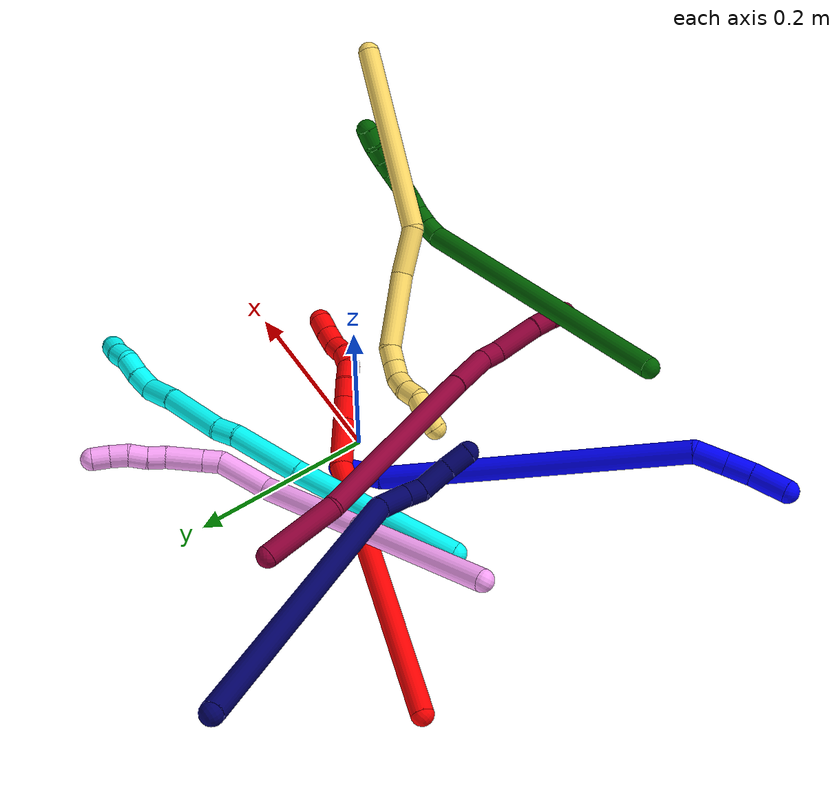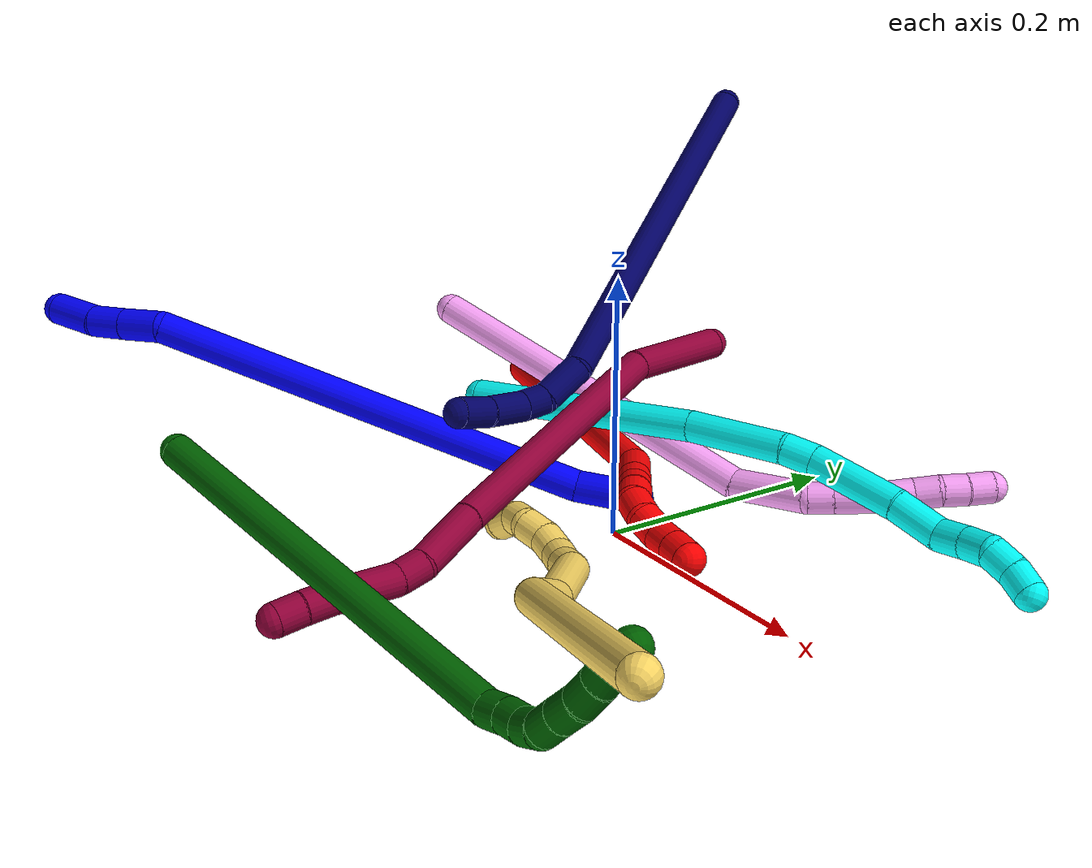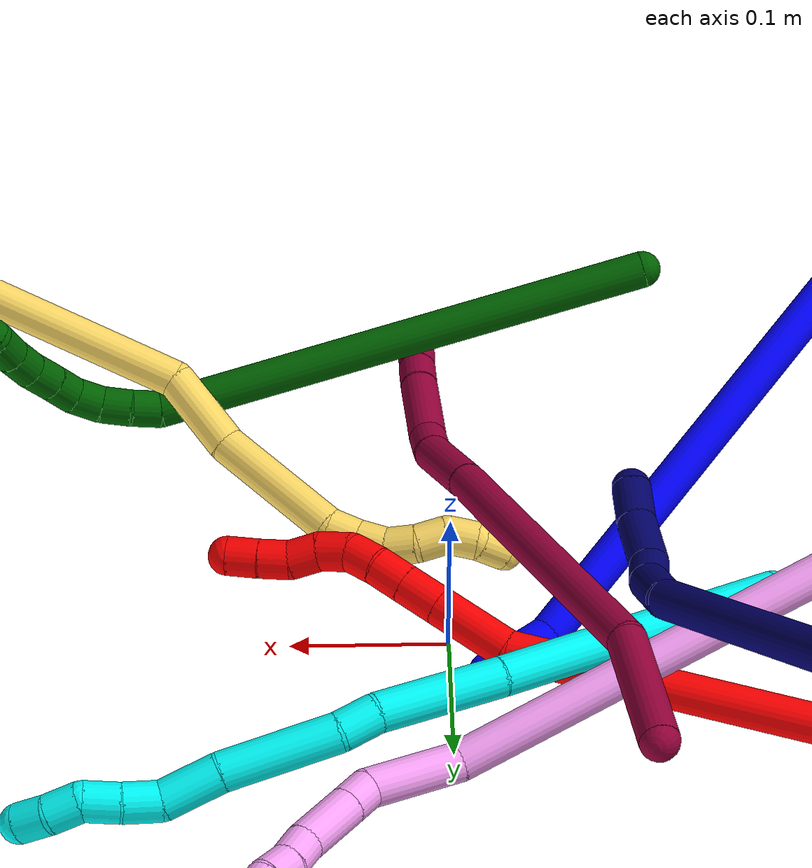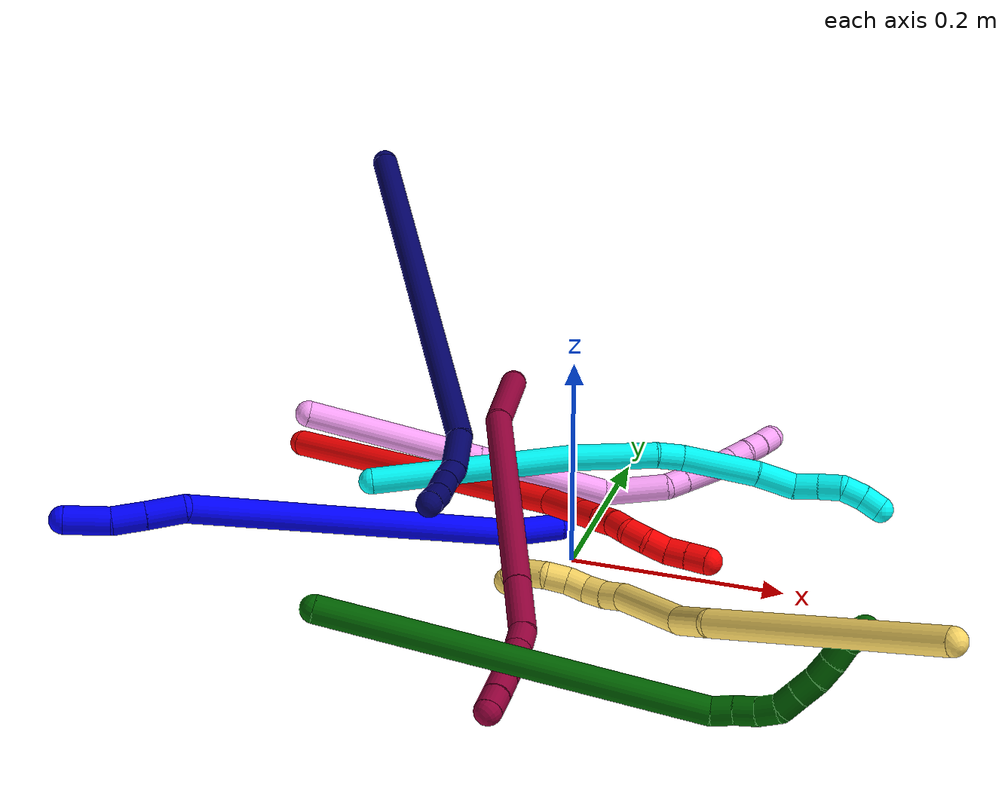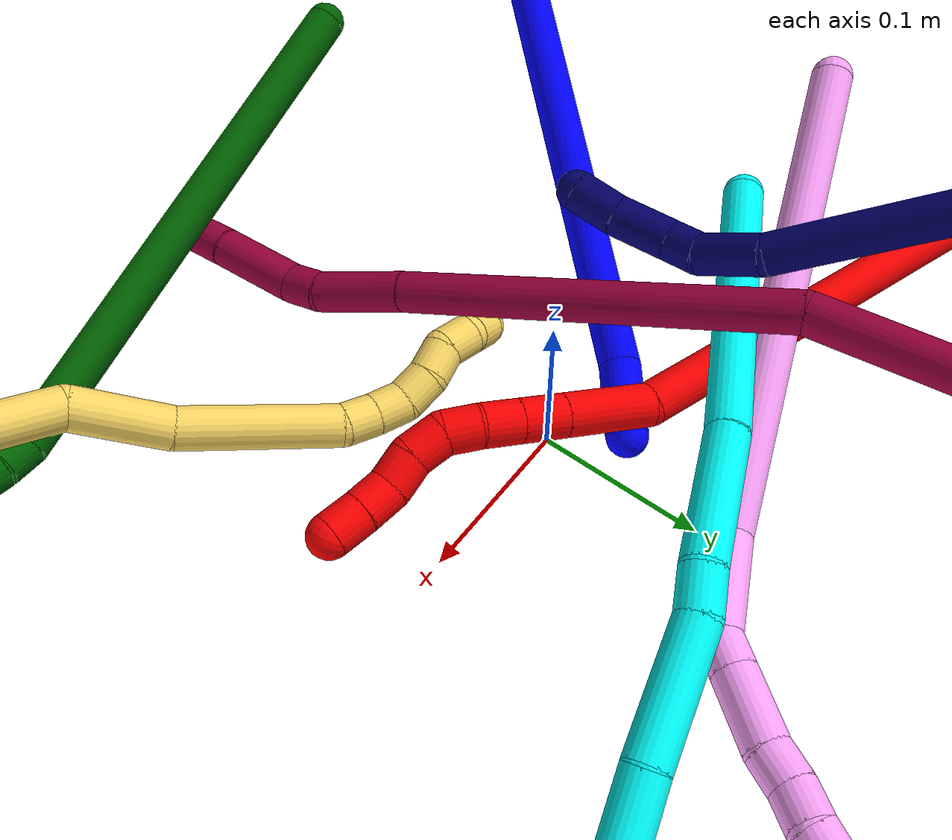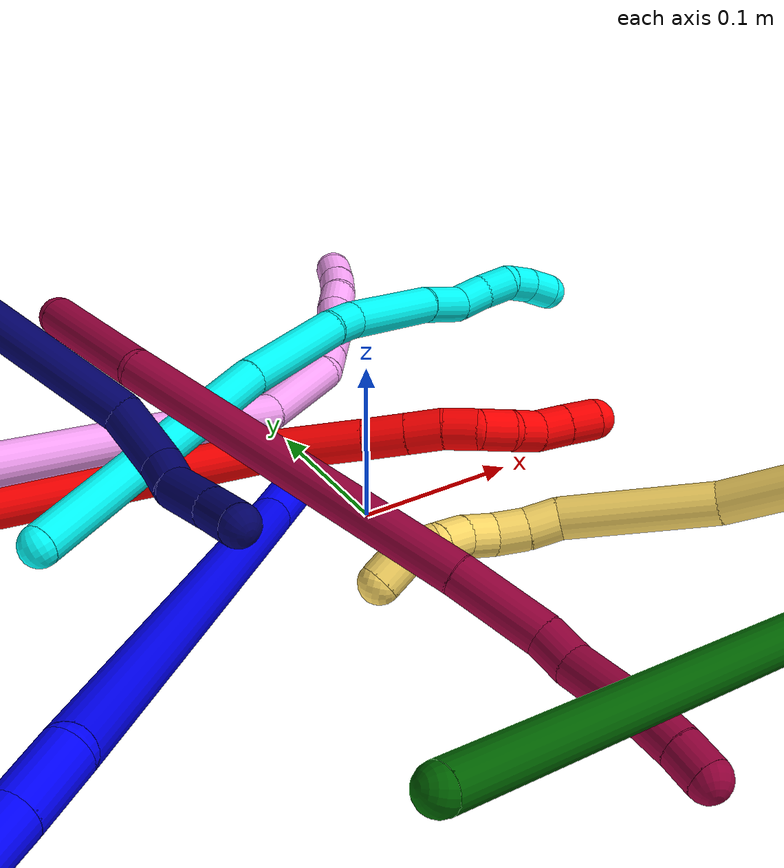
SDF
<sdf version="1.7">
 <world name="default">
  <plugin name="TubeGeneratorPlugin" filename="libtube_generator_plugin.so"/>
  <model name="photoneo_s_sensor">
   <static>1</static>
   <pose>0 0 2 1.57079 1.57079 3.14159</pose>
   <link name="link">
    <inertial><mass>0.1</mass></inertial>
    <sensor name="sensor" type="depth">
     <update_rate>30</update_rate>
     <camera>
      <horizontal_fov>1.22</horizontal_fov>
      <image><width>1920</width><height>1200</height><format>B8G8R8</format></image>
      <clip><near>0.1</near><far>4</far></clip>
      <depth_camera><output>points</output></depth_camera>
     </camera>
     <plugin name="camera_plugin" filename="libgazebo_ros_depth_camera.so">
      <baseline>0.2</baseline>
      <alwaysOn>1</alwaysOn>
      <updateRate>0.0</updateRate>
      <cameraName>camera_ir</cameraName>
      <imageTopicName>/camera/color/image_raw</imageTopicName>
      <cameraInfoTopicName>/camera/color/camera_info</cameraInfoTopicName>
      <depthImageTopicName>/camera/depth/image_raw</depthImageTopicName>
      <depthImageCameraInfoTopicName>/camera/depth/camera_info</depthImageCameraInfoTopicName>
      <pointCloudTopicName>/camera/depth/points</pointCloudTopicName>
      <frameName>fr_optical</frameName>
      <pointCloudCutoff>0.1</pointCloudCutoff>
      <pointCloudCutoffMax>2.0</pointCloudCutoffMax>
      <distortionK1>0</distortionK1>
      <distortionK2>0</distortionK2>
      <distortionK3>0</distortionK3>
      <distortionT1>0</distortionT1>
      <distortionT2>0</distortionT2>
      <CxPrime>0</CxPrime>
      <Cx>0</Cx>
      <Cy>0</Cy>
      <focalLength>0</focalLength>
      <hackBaseline>0</hackBaseline>
     </plugin>
    </sensor>
   </link>
  </model>
  <gravity>0 0 -9.8</gravity>
  <magnetic_field>6e-06 2.3e-05 -4.2e-05</magnetic_field>
  <atmosphere type="adiabatic"/>
  <physics name="default_physics" default="0" type="ode">
   <max_step_size>0.003</max_step_size>
   <real_time_factor>1</real_time_factor>
   <real_time_update_rate>1000</real_time_update_rate>
   <max_contacts>10000</max_contacts>
   <ode>
    <solver>
     <type>quick</type>
     <iters>100</iters>
     <sor>1.3</sor>
     <use_dynamic_moi_rescaling>0</use_dynamic_moi_rescaling>
    </solver>
    <constraints>
     <contact_max_correcting_vel>0</contact_max_correcting_vel>
     <contact_surface_layer>0.001</contact_surface_layer>
     <cfm>0</cfm>
     <erp>0.2</erp>
    </constraints>
   </ode>
  </physics>
  <scene><ambient>0.4 0.4 0.4 1</ambient><background>0.7 0.7 0.7 1</background><shadows>0</shadows></scene>
  <audio><device>default</device></audio>
  <spherical_coordinates>
   <surface_model>EARTH_WGS84</surface_model>
   <latitude_deg>0</latitude_deg>
   <longitude_deg>0</longitude_deg>
   <elevation>0</elevation>
   <heading_deg>0</heading_deg>
  </spherical_coordinates>
  <model name="bin">
   <static>1</static>
   <link name="bottom">
    <collision name="collision-bottom">
     <pose>0 0 -0.01 0 -0 0</pose>
     <geometry><box><size>0.8 0.6 0.02</size></box></geometry>
     <surface>
      <friction><ode><mu>100</mu><mu2>100</mu2></ode></friction>
      <contact><collide_bitmask>65535</collide_bitmask></contact>
     </surface>
    </collision>
   </link>
   <link name="west_wall">
    <collision name="collision-west_wall">
     <pose>-0.41 0 0.1 0 -0 0</pose>
     <geometry><box><size>0.02 0.6 0.2</size></box></geometry>
     <surface>
      <friction><ode><mu>100</mu><mu2>100</mu2></ode></friction>
      <contact><collide_bitmask>65535</collide_bitmask></contact>
     </surface>
    </collision>
   </link>
   <link name="east_wall">
    <collision name="collision-east_wall">
     <pose>0.41 0 0.1 0 -0 0</pose>
     <geometry><box><size>0.02 0.6 0.2</size></box></geometry>
     <surface>
      <friction><ode><mu>100</mu><mu2>100</mu2></ode></friction>
      <contact><collide_bitmask>65535</collide_bitmask></contact>
     </surface>
    </collision>
   </link>
   <link name="south_wall">
    <collision name="collision-south_wall">
     <pose>0 -0.31 0.1 0 -0 0</pose>
     <geometry><box><size>0.8 0.02 0.2</size></box></geometry>
     <surface>
      <friction><ode><mu>100</mu><mu2>100</mu2></ode></friction>
      <contact><collide_bitmask>65535</collide_bitmask></contact>
     </surface>
    </collision>
   </link>
   <link name="north_wall">
    <collision name="collision-north_wall">
     <pose>0 0.31 0.1 0 -0 0</pose>
     <geometry><box><size>0.8 0.02 0.2</size></box></geometry>
     <surface>
      <friction><ode><mu>100</mu><mu2>100</mu2></ode></friction>
      <contact><collide_bitmask>65535</collide_bitmask></contact>
     </surface>
    </collision>
   </link>
  </model>
  <model name="1">
   <static>0</static>
   <link name="1">
    <collision name="collision-cylinder-e_1_1_4">
     <pose>-0.003028 -0.002243 -0.01988 3.02926 -0.15021 -1.85819</pose>
     <geometry><cylinder><radius>0.0125</radius><length>0.040468</length></cylinder></geometry>
     <surface>
      <friction><ode><mu>1.16</mu><mu2>1.16</mu2><slip1>0</slip1><slip2>0</slip2></ode></friction>
      <contact><ode><kp>1e+06</kp><kd>1</kd><max_vel>0</max_vel><min_depth>0.001</min_depth></ode></contact>
     </surface>
    </collision>
    <visual name="visual-cylinder-e_1_1_4">
     <pose>-0.003028 -0.002243 -0.01988 3.02926 -0.15021 -1.85819</pose>
     <geometry><cylinder><radius>0.0125</radius><length>0.040468</length></cylinder></geometry>
     <material><ambient>0 0 1 1</ambient></material>
    </visual>
    <collision name="collision-cylinder-e_2_4_5">
     <pose>-0.005324 -0.006851 -0.054145 2.97861 0.050154 0.595919</pose>
     <geometry><cylinder><radius>0.0125</radius><length>0.029194</length></cylinder></geometry>
     <surface>
      <friction><ode><mu>1.16</mu><mu2>1.16</mu2><slip1>0</slip1><slip2>0</slip2></ode></friction>
      <contact><ode><kp>1e+06</kp><kd>1</kd><max_vel>0</max_vel><min_depth>0.001</min_depth></ode></contact>
     </surface>
    </collision>
    <visual name="visual-cylinder-e_2_4_5">
     <pose>-0.005324 -0.006851 -0.054145 2.97861 0.050154 0.595919</pose>
     <geometry><cylinder><radius>0.0125</radius><length>0.029194</length></cylinder></geometry>
     <material><ambient>0 0 1 1</ambient></material>
    </visual>
    <collision name="collision-cylinder-e_3_5_6">
     <pose>-0.003384 -0.012129 -0.085321 2.96984 0.07076 0.780155</pose>
     <geometry><cylinder><radius>0.0125</radius><length>0.034168</length></cylinder></geometry>
     <surface>
      <friction><ode><mu>1.16</mu><mu2>1.16</mu2><slip1>0</slip1><slip2>0</slip2></ode></friction>
      <contact><ode><kp>1e+06</kp><kd>1</kd><max_vel>0</max_vel><min_depth>0.001</min_depth></ode></contact>
     </surface>
    </collision>
    <visual name="visual-cylinder-e_3_5_6">
     <pose>-0.003384 -0.012129 -0.085321 2.96984 0.07076 0.780155</pose>
     <geometry><cylinder><radius>0.0125</radius><length>0.034168</length></cylinder></geometry>
     <material><ambient>0 0 1 1</ambient></material>
    </visual>
    <collision name="collision-cylinder-e_4_6_7">
     <pose>0.026494 0.037502 -0.265271 -2.83005 0.165726 -0.972915</pose>
     <geometry><cylinder><radius>0.0125</radius><length>0.347586</length></cylinder></geometry>
     <surface>
      <friction><ode><mu>1.16</mu><mu2>1.16</mu2><slip1>0</slip1><slip2>0</slip2></ode></friction>
      <contact><ode><kp>1e+06</kp><kd>1</kd><max_vel>0</max_vel><min_depth>0.001</min_depth></ode></contact>
     </surface>
    </collision>
    <visual name="visual-cylinder-e_4_6_7">
     <pose>0.026494 0.037502 -0.265271 -2.83005 0.165726 -0.972915</pose>
     <geometry><cylinder><radius>0.0125</radius><length>0.347586</length></cylinder></geometry>
     <material><ambient>0 0 1 1</ambient></material>
    </visual>
    <collision name="collision-cylinder-e_5_7_2">
     <pose>0.057982 0.089597 -0.452555 3.12303 0.116264 2.82533</pose>
     <geometry><cylinder><radius>0.0125</radius><length>0.048585</length></cylinder></geometry>
     <surface>
      <friction><ode><mu>1.16</mu><mu2>1.16</mu2><slip1>0</slip1><slip2>0</slip2></ode></friction>
      <contact><ode><kp>1e+06</kp><kd>1</kd><max_vel>0</max_vel><min_depth>0.001</min_depth></ode></contact>
     </surface>
    </collision>
    <visual name="visual-cylinder-e_5_7_2">
     <pose>0.057982 0.089597 -0.452555 3.12303 0.116264 2.82533</pose>
     <geometry><cylinder><radius>0.0125</radius><length>0.048585</length></cylinder></geometry>
     <material><ambient>0 0 1 1</ambient></material>
    </visual>
    <collision name="collision-sphere-2">
     <pose>0.0608 0.08915 -0.47668 0 -0 0</pose>
     <geometry><sphere><radius>0.0125</radius></sphere></geometry>
     <surface>
      <friction><ode><mu>1.16</mu><mu2>1.16</mu2><slip1>0</slip1><slip2>0</slip2></ode></friction>
      <contact><ode><kp>1e+06</kp><kd>1</kd><max_vel>0</max_vel><min_depth>0.001</min_depth></ode></contact>
     </surface>
    </collision>
    <visual name="visual-sphere-2">
     <pose>0.0608 0.08915 -0.47668 0 -0 0</pose>
     <geometry><sphere><radius>0.0125</radius></sphere></geometry>
     <material><ambient>0 0 1 1</ambient></material>
    </visual>
    <collision name="collision-sphere-7">
     <pose>0.055164 0.090045 -0.428431 0 -0 0</pose>
     <geometry><sphere><radius>0.0125</radius></sphere></geometry>
     <surface>
      <friction><ode><mu>1.16</mu><mu2>1.16</mu2><slip1>0</slip1><slip2>0</slip2></ode></friction>
      <contact><ode><kp>1e+06</kp><kd>1</kd><max_vel>0</max_vel><min_depth>0.001</min_depth></ode></contact>
     </surface>
    </collision>
    <visual name="visual-sphere-7">
     <pose>0.055164 0.090045 -0.428431 0 -0 0</pose>
     <geometry><sphere><radius>0.0125</radius></sphere></geometry>
     <material><ambient>0 0 1 1</ambient></material>
    </visual>
    <collision name="collision-sphere-6">
     <pose>-0.002177 -0.015041 -0.102111 0 -0 0</pose>
     <geometry><sphere><radius>0.0125</radius></sphere></geometry>
     <surface>
      <friction><ode><mu>1.16</mu><mu2>1.16</mu2><slip1>0</slip1><slip2>0</slip2></ode></friction>
      <contact><ode><kp>1e+06</kp><kd>1</kd><max_vel>0</max_vel><min_depth>0.001</min_depth></ode></contact>
     </surface>
    </collision>
    <visual name="visual-sphere-6">
     <pose>-0.002177 -0.015041 -0.102111 0 -0 0</pose>
     <geometry><sphere><radius>0.0125</radius></sphere></geometry>
     <material><ambient>0 0 1 1</ambient></material>
    </visual>
    <collision name="collision-sphere-5">
     <pose>-0.004592 -0.009216 -0.06853 0 -0 0</pose>
     <geometry><sphere><radius>0.0125</radius></sphere></geometry>
     <surface>
      <friction><ode><mu>1.16</mu><mu2>1.16</mu2><slip1>0</slip1><slip2>0</slip2></ode></friction>
      <contact><ode><kp>1e+06</kp><kd>1</kd><max_vel>0</max_vel><min_depth>0.001</min_depth></ode></contact>
     </surface>
    </collision>
    <visual name="visual-sphere-5">
     <pose>-0.004592 -0.009216 -0.06853 0 -0 0</pose>
     <geometry><sphere><radius>0.0125</radius></sphere></geometry>
     <material><ambient>0 0 1 1</ambient></material>
    </visual>
    <collision name="collision-sphere-1">
     <geometry><sphere><radius>0.0125</radius></sphere></geometry>
     <surface>
      <friction><ode><mu>1.16</mu><mu2>1.16</mu2><slip1>0</slip1><slip2>0</slip2></ode></friction>
      <contact><ode><kp>1e+06</kp><kd>1</kd><max_vel>0</max_vel><min_depth>0.001</min_depth></ode></contact>
     </surface>
    </collision>
    <visual name="visual-sphere-1">
     <geometry><sphere><radius>0.0125</radius></sphere></geometry>
     <material><ambient>0 0 1 1</ambient></material>
    </visual>
    <collision name="collision-sphere-4">
     <pose>-0.006056 -0.004485 -0.03976 0 -0 0</pose>
     <geometry><sphere><radius>0.0125</radius></sphere></geometry>
     <surface>
      <friction><ode><mu>1.16</mu><mu2>1.16</mu2><slip1>0</slip1><slip2>0</slip2></ode></friction>
      <contact><ode><kp>1e+06</kp><kd>1</kd><max_vel>0</max_vel><min_depth>0.001</min_depth></ode></contact>
     </surface>
    </collision>
    <visual name="visual-sphere-4">
     <pose>-0.006056 -0.004485 -0.03976 0 -0 0</pose>
     <geometry><sphere><radius>0.0125</radius></sphere></geometry>
     <material><ambient>0 0 1 1</ambient></material>
    </visual>
    <inertial>
     <pose>0.023265 0.033366 -0.238985 0 -0 0</pose>
     <mass>0.5</mass>
     <inertia>
      <ixx>-0.000914</ixx>
      <ixy>0</ixy>
      <ixz>0</ixz>
      <iyy>-0.004583</iyy>
      <iyz>0</iyz>
      <izz>-0.001677</izz>
     </inertia>
    </inertial>
   </link>
   <pose>-0.366515 -0.288501 0.128952 -1.44092 -0.374679 2.09561</pose>
  </model>
  <model name="2">
   <static>0</static>
   <link name="2">
    <collision name="collision-cylinder-e_1_1_4">
     <pose>0.12537 -0.030789 -0.075246 2.7532 0.995482 2.44703</pose>
     <geometry><cylinder><radius>0.0125</radius><length>0.298848</length></cylinder></geometry>
     <surface>
      <friction><ode><mu>1.16</mu><mu2>1.16</mu2><slip1>0</slip1><slip2>0</slip2></ode></friction>
      <contact><ode><kp>1e+06</kp><kd>1</kd><max_vel>0</max_vel><min_depth>0.001</min_depth></ode></contact>
     </surface>
    </collision>
    <visual name="visual-cylinder-e_1_1_4">
     <pose>0.12537 -0.030789 -0.075246 2.7532 0.995482 2.44703</pose>
     <geometry><cylinder><radius>0.0125</radius><length>0.298848</length></cylinder></geometry>
     <material><ambient>1 0 0 1</ambient></material>
    </visual>
    <collision name="collision-cylinder-e_2_4_5">
     <pose>0.266268 -0.066424 -0.170646 2.90559 0.64295 2.4576</pose>
     <geometry><cylinder><radius>0.0125</radius><length>0.051799</length></cylinder></geometry>
     <surface>
      <friction><ode><mu>1.16</mu><mu2>1.16</mu2><slip1>0</slip1><slip2>0</slip2></ode></friction>
      <contact><ode><kp>1e+06</kp><kd>1</kd><max_vel>0</max_vel><min_depth>0.001</min_depth></ode></contact>
     </surface>
    </collision>
    <visual name="visual-cylinder-e_2_4_5">
     <pose>0.266268 -0.066424 -0.170646 2.90559 0.64295 2.4576</pose>
     <geometry><cylinder><radius>0.0125</radius><length>0.051799</length></cylinder></geometry>
     <material><ambient>1 0 0 1</ambient></material>
    </visual>
    <collision name="collision-cylinder-e_3_5_6">
     <pose>0.289605 -0.073838 -0.200866 2.89189 0.644505 2.4225</pose>
     <geometry><cylinder><radius>0.0125</radius><length>0.025992</length></cylinder></geometry>
     <surface>
      <friction><ode><mu>1.16</mu><mu2>1.16</mu2><slip1>0</slip1><slip2>0</slip2></ode></friction>
      <contact><ode><kp>1e+06</kp><kd>1</kd><max_vel>0</max_vel><min_depth>0.001</min_depth></ode></contact>
     </surface>
    </collision>
    <visual name="visual-cylinder-e_3_5_6">
     <pose>0.289605 -0.073838 -0.200866 2.89189 0.644505 2.4225</pose>
     <geometry><cylinder><radius>0.0125</radius><length>0.025992</length></cylinder></geometry>
     <material><ambient>1 0 0 1</ambient></material>
    </visual>
    <collision name="collision-cylinder-e_4_6_7">
     <pose>0.304021 -0.078612 -0.21948 2.8889 0.642608 2.41243</pose>
     <geometry><cylinder><radius>0.0125</radius><length>0.022053</length></cylinder></geometry>
     <surface>
      <friction><ode><mu>1.16</mu><mu2>1.16</mu2><slip1>0</slip1><slip2>0</slip2></ode></friction>
      <contact><ode><kp>1e+06</kp><kd>1</kd><max_vel>0</max_vel><min_depth>0.001</min_depth></ode></contact>
     </surface>
    </collision>
    <visual name="visual-cylinder-e_4_6_7">
     <pose>0.304021 -0.078612 -0.21948 2.8889 0.642608 2.41243</pose>
     <geometry><cylinder><radius>0.0125</radius><length>0.022053</length></cylinder></geometry>
     <material><ambient>1 0 0 1</ambient></material>
    </visual>
    <collision name="collision-cylinder-e_5_7_8">
     <pose>0.317147 -0.081221 -0.235951 3.09089 0.687675 3.0002</pose>
     <geometry><cylinder><radius>0.0125</radius><length>0.020537</length></cylinder></geometry>
     <surface>
      <friction><ode><mu>1.16</mu><mu2>1.16</mu2><slip1>0</slip1><slip2>0</slip2></ode></friction>
      <contact><ode><kp>1e+06</kp><kd>1</kd><max_vel>0</max_vel><min_depth>0.001</min_depth></ode></contact>
     </surface>
    </collision>
    <visual name="visual-cylinder-e_5_7_8">
     <pose>0.317147 -0.081221 -0.235951 3.09089 0.687675 3.0002</pose>
     <geometry><cylinder><radius>0.0125</radius><length>0.020537</length></cylinder></geometry>
     <material><ambient>1 0 0 1</ambient></material>
    </visual>
    <collision name="collision-cylinder-e_6_8_9">
     <pose>0.332954 -0.081222 -0.248404 -3.0531 1.11572 -2.99992</pose>
     <geometry><cylinder><radius>0.0125</radius><length>0.020684</length></cylinder></geometry>
     <surface>
      <friction><ode><mu>1.16</mu><mu2>1.16</mu2><slip1>0</slip1><slip2>0</slip2></ode></friction>
      <contact><ode><kp>1e+06</kp><kd>1</kd><max_vel>0</max_vel><min_depth>0.001</min_depth></ode></contact>
     </surface>
    </collision>
    <visual name="visual-cylinder-e_6_8_9">
     <pose>0.332954 -0.081222 -0.248404 -3.0531 1.11572 -2.99992</pose>
     <geometry><cylinder><radius>0.0125</radius><length>0.020684</length></cylinder></geometry>
     <material><ambient>1 0 0 1</ambient></material>
    </visual>
    <collision name="collision-cylinder-e_7_9_10">
     <pose>0.352125 -0.079848 -0.254174 -2.47766 1.41251 -2.37349</pose>
     <geometry><cylinder><radius>0.0125</radius><length>0.020012</length></cylinder></geometry>
     <surface>
      <friction><ode><mu>1.16</mu><mu2>1.16</mu2><slip1>0</slip1><slip2>0</slip2></ode></friction>
      <contact><ode><kp>1e+06</kp><kd>1</kd><max_vel>0</max_vel><min_depth>0.001</min_depth></ode></contact>
     </surface>
    </collision>
    <visual name="visual-cylinder-e_7_9_10">
     <pose>0.352125 -0.079848 -0.254174 -2.47766 1.41251 -2.37349</pose>
     <geometry><cylinder><radius>0.0125</radius><length>0.020012</length></cylinder></geometry>
     <material><ambient>1 0 0 1</ambient></material>
    </visual>
    <collision name="collision-cylinder-e_8_10_11">
     <pose>0.371278 -0.080564 -0.258786 2.67738 1.18473 2.46607</pose>
     <geometry><cylinder><radius>0.0125</radius><length>0.020019</length></cylinder></geometry>
     <surface>
      <friction><ode><mu>1.16</mu><mu2>1.16</mu2><slip1>0</slip1><slip2>0</slip2></ode></friction>
      <contact><ode><kp>1e+06</kp><kd>1</kd><max_vel>0</max_vel><min_depth>0.001</min_depth></ode></contact>
     </surface>
    </collision>
    <visual name="visual-cylinder-e_8_10_11">
     <pose>0.371278 -0.080564 -0.258786 2.67738 1.18473 2.46607</pose>
     <geometry><cylinder><radius>0.0125</radius><length>0.020019</length></cylinder></geometry>
     <material><ambient>1 0 0 1</ambient></material>
    </visual>
    <collision name="collision-cylinder-e_9_11_2">
     <pose>0.389657 -0.083866 -0.266033 2.74685 1.13867 2.53593</pose>
     <geometry><cylinder><radius>0.0125</radius><length>0.020056</length></cylinder></geometry>
     <surface>
      <friction><ode><mu>1.16</mu><mu2>1.16</mu2><slip1>0</slip1><slip2>0</slip2></ode></friction>
      <contact><ode><kp>1e+06</kp><kd>1</kd><max_vel>0</max_vel><min_depth>0.001</min_depth></ode></contact>
     </surface>
    </collision>
    <visual name="visual-cylinder-e_9_11_2">
     <pose>0.389657 -0.083866 -0.266033 2.74685 1.13867 2.53593</pose>
     <geometry><cylinder><radius>0.0125</radius><length>0.020056</length></cylinder></geometry>
     <material><ambient>1 0 0 1</ambient></material>
    </visual>
    <collision name="collision-sphere-2">
     <pose>0.398763 -0.085481 -0.26991 0 -0 0</pose>
     <geometry><sphere><radius>0.0125</radius></sphere></geometry>
     <surface>
      <friction><ode><mu>1.16</mu><mu2>1.16</mu2><slip1>0</slip1><slip2>0</slip2></ode></friction>
      <contact><ode><kp>1e+06</kp><kd>1</kd><max_vel>0</max_vel><min_depth>0.001</min_depth></ode></contact>
     </surface>
    </collision>
    <visual name="visual-sphere-2">
     <pose>0.398763 -0.085481 -0.26991 0 -0 0</pose>
     <geometry><sphere><radius>0.0125</radius></sphere></geometry>
     <material><ambient>1 0 0 1</ambient></material>
    </visual>
    <collision name="collision-sphere-11">
     <pose>0.38055 -0.082251 -0.262156 0 -0 0</pose>
     <geometry><sphere><radius>0.0125</radius></sphere></geometry>
     <surface>
      <friction><ode><mu>1.16</mu><mu2>1.16</mu2><slip1>0</slip1><slip2>0</slip2></ode></friction>
      <contact><ode><kp>1e+06</kp><kd>1</kd><max_vel>0</max_vel><min_depth>0.001</min_depth></ode></contact>
     </surface>
    </collision>
    <visual name="visual-sphere-11">
     <pose>0.38055 -0.082251 -0.262156 0 -0 0</pose>
     <geometry><sphere><radius>0.0125</radius></sphere></geometry>
     <material><ambient>1 0 0 1</ambient></material>
    </visual>
    <collision name="collision-sphere-10">
     <pose>0.362005 -0.078876 -0.255416 0 -0 0</pose>
     <geometry><sphere><radius>0.0125</radius></sphere></geometry>
     <surface>
      <friction><ode><mu>1.16</mu><mu2>1.16</mu2><slip1>0</slip1><slip2>0</slip2></ode></friction>
      <contact><ode><kp>1e+06</kp><kd>1</kd><max_vel>0</max_vel><min_depth>0.001</min_depth></ode></contact>
     </surface>
    </collision>
    <visual name="visual-sphere-10">
     <pose>0.362005 -0.078876 -0.255416 0 -0 0</pose>
     <geometry><sphere><radius>0.0125</radius></sphere></geometry>
     <material><ambient>1 0 0 1</ambient></material>
    </visual>
    <collision name="collision-sphere-9">
     <pose>0.342244 -0.08082 -0.252932 0 -0 0</pose>
     <geometry><sphere><radius>0.0125</radius></sphere></geometry>
     <surface>
      <friction><ode><mu>1.16</mu><mu2>1.16</mu2><slip1>0</slip1><slip2>0</slip2></ode></friction>
      <contact><ode><kp>1e+06</kp><kd>1</kd><max_vel>0</max_vel><min_depth>0.001</min_depth></ode></contact>
     </surface>
    </collision>
    <visual name="visual-sphere-9">
     <pose>0.342244 -0.08082 -0.252932 0 -0 0</pose>
     <geometry><sphere><radius>0.0125</radius></sphere></geometry>
     <material><ambient>1 0 0 1</ambient></material>
    </visual>
    <collision name="collision-sphere-4">
     <pose>0.25074 -0.061577 -0.150492 0 -0 0</pose>
     <geometry><sphere><radius>0.0125</radius></sphere></geometry>
     <surface>
      <friction><ode><mu>1.16</mu><mu2>1.16</mu2><slip1>0</slip1><slip2>0</slip2></ode></friction>
      <contact><ode><kp>1e+06</kp><kd>1</kd><max_vel>0</max_vel><min_depth>0.001</min_depth></ode></contact>
     </surface>
    </collision>
    <visual name="visual-sphere-4">
     <pose>0.25074 -0.061577 -0.150492 0 -0 0</pose>
     <geometry><sphere><radius>0.0125</radius></sphere></geometry>
     <material><ambient>1 0 0 1</ambient></material>
    </visual>
    <collision name="collision-sphere-1">
     <geometry><sphere><radius>0.0125</radius></sphere></geometry>
     <surface>
      <friction><ode><mu>1.16</mu><mu2>1.16</mu2><slip1>0</slip1><slip2>0</slip2></ode></friction>
      <contact><ode><kp>1e+06</kp><kd>1</kd><max_vel>0</max_vel><min_depth>0.001</min_depth></ode></contact>
     </surface>
    </collision>
    <visual name="visual-sphere-1">
     <geometry><sphere><radius>0.0125</radius></sphere></geometry>
     <material><ambient>1 0 0 1</ambient></material>
    </visual>
    <collision name="collision-sphere-8">
     <pose>0.323665 -0.081624 -0.243876 0 -0 0</pose>
     <geometry><sphere><radius>0.0125</radius></sphere></geometry>
     <surface>
      <friction><ode><mu>1.16</mu><mu2>1.16</mu2><slip1>0</slip1><slip2>0</slip2></ode></friction>
      <contact><ode><kp>1e+06</kp><kd>1</kd><max_vel>0</max_vel><min_depth>0.001</min_depth></ode></contact>
     </surface>
    </collision>
    <visual name="visual-sphere-8">
     <pose>0.323665 -0.081624 -0.243876 0 -0 0</pose>
     <geometry><sphere><radius>0.0125</radius></sphere></geometry>
     <material><ambient>1 0 0 1</ambient></material>
    </visual>
    <collision name="collision-sphere-5">
     <pose>0.281797 -0.071271 -0.190799 0 -0 0</pose>
     <geometry><sphere><radius>0.0125</radius></sphere></geometry>
     <surface>
      <friction><ode><mu>1.16</mu><mu2>1.16</mu2><slip1>0</slip1><slip2>0</slip2></ode></friction>
      <contact><ode><kp>1e+06</kp><kd>1</kd><max_vel>0</max_vel><min_depth>0.001</min_depth></ode></contact>
     </surface>
    </collision>
    <visual name="visual-sphere-5">
     <pose>0.281797 -0.071271 -0.190799 0 -0 0</pose>
     <geometry><sphere><radius>0.0125</radius></sphere></geometry>
     <material><ambient>1 0 0 1</ambient></material>
    </visual>
    <collision name="collision-sphere-6">
     <pose>0.297413 -0.076405 -0.210933 0 -0 0</pose>
     <geometry><sphere><radius>0.0125</radius></sphere></geometry>
     <surface>
      <friction><ode><mu>1.16</mu><mu2>1.16</mu2><slip1>0</slip1><slip2>0</slip2></ode></friction>
      <contact><ode><kp>1e+06</kp><kd>1</kd><max_vel>0</max_vel><min_depth>0.001</min_depth></ode></contact>
     </surface>
    </collision>
    <visual name="visual-sphere-6">
     <pose>0.297413 -0.076405 -0.210933 0 -0 0</pose>
     <geometry><sphere><radius>0.0125</radius></sphere></geometry>
     <material><ambient>1 0 0 1</ambient></material>
    </visual>
    <collision name="collision-sphere-7">
     <pose>0.310629 -0.080819 -0.228027 0 -0 0</pose>
     <geometry><sphere><radius>0.0125</radius></sphere></geometry>
     <surface>
      <friction><ode><mu>1.16</mu><mu2>1.16</mu2><slip1>0</slip1><slip2>0</slip2></ode></friction>
      <contact><ode><kp>1e+06</kp><kd>1</kd><max_vel>0</max_vel><min_depth>0.001</min_depth></ode></contact>
     </surface>
    </collision>
    <visual name="visual-sphere-7">
     <pose>0.310629 -0.080819 -0.228027 0 -0 0</pose>
     <geometry><sphere><radius>0.0125</radius></sphere></geometry>
     <material><ambient>1 0 0 1</ambient></material>
    </visual>
    <inertial>
     <pose>0.20237 -0.049071 -0.133948 0 -0 0</pose>
     <mass>0.5</mass>
     <inertia>
      <ixx>-0.000129</ixx>
      <ixy>0</ixy>
      <ixz>0</ixz>
      <iyy>0.002849</iyy>
      <iyz>0</iyz>
      <izz>-0.00145</izz>
     </inertia>
    </inertial>
   </link>
   <pose>-0.320396 0.128154 0.011868 -1.82203 0.286654 0.166579</pose>
  </model>
  <model name="3">
   <static>0</static>
   <link name="3">
    <collision name="collision-cylinder-e_1_1_4">
     <pose>0.07109 0.065069 0.006093 -1.47742 0.827418 -0.760761</pose>
     <geometry><cylinder><radius>0.0125</radius><length>0.19313</length></cylinder></geometry>
     <surface>
      <friction><ode><mu>1.16</mu><mu2>1.16</mu2><slip1>0</slip1><slip2>0</slip2></ode></friction>
      <contact><ode><kp>1e+06</kp><kd>1</kd><max_vel>0</max_vel><min_depth>0.001</min_depth></ode></contact>
     </surface>
    </collision>
    <visual name="visual-cylinder-e_1_1_4">
     <pose>0.07109 0.065069 0.006093 -1.47742 0.827418 -0.760761</pose>
     <geometry><cylinder><radius>0.0125</radius><length>0.19313</length></cylinder></geometry>
     <material><ambient>0.003922 1 0.996078 1</ambient></material>
    </visual>
    <collision name="collision-cylinder-e_2_4_5">
     <pose>0.17306 0.156386 0.011017 -1.61534 0.865801 -0.900223</pose>
     <geometry><cylinder><radius>0.0125</radius><length>0.081093</length></cylinder></geometry>
     <surface>
      <friction><ode><mu>1.16</mu><mu2>1.16</mu2><slip1>0</slip1><slip2>0</slip2></ode></friction>
      <contact><ode><kp>1e+06</kp><kd>1</kd><max_vel>0</max_vel><min_depth>0.001</min_depth></ode></contact>
     </surface>
    </collision>
    <visual name="visual-cylinder-e_2_4_5">
     <pose>0.17306 0.156386 0.011017 -1.61534 0.865801 -0.900223</pose>
     <geometry><cylinder><radius>0.0125</radius><length>0.081093</length></cylinder></geometry>
     <material><ambient>0.003922 1 0.996078 1</ambient></material>
    </visual>
    <collision name="collision-cylinder-e_3_5_6">
     <pose>0.211894 0.192304 0.008285 -1.73095 0.682062 -0.789852</pose>
     <geometry><cylinder><radius>0.0125</radius><length>0.025233</length></cylinder></geometry>
     <surface>
      <friction><ode><mu>1.16</mu><mu2>1.16</mu2><slip1>0</slip1><slip2>0</slip2></ode></friction>
      <contact><ode><kp>1e+06</kp><kd>1</kd><max_vel>0</max_vel><min_depth>0.001</min_depth></ode></contact>
     </surface>
    </collision>
    <visual name="visual-cylinder-e_3_5_6">
     <pose>0.211894 0.192304 0.008285 -1.73095 0.682062 -0.789852</pose>
     <geometry><cylinder><radius>0.0125</radius><length>0.025233</length></cylinder></geometry>
     <material><ambient>0.003922 1 0.996078 1</ambient></material>
    </visual>
    <collision name="collision-cylinder-e_4_6_7">
     <pose>0.246817 0.225079 -0.003157 -1.97488 0.82068 -1.16559</pose>
     <geometry><cylinder><radius>0.0125</radius><length>0.073725</length></cylinder></geometry>
     <surface>
      <friction><ode><mu>1.16</mu><mu2>1.16</mu2><slip1>0</slip1><slip2>0</slip2></ode></friction>
      <contact><ode><kp>1e+06</kp><kd>1</kd><max_vel>0</max_vel><min_depth>0.001</min_depth></ode></contact>
     </surface>
    </collision>
    <visual name="visual-cylinder-e_4_6_7">
     <pose>0.246817 0.225079 -0.003157 -1.97488 0.82068 -1.16559</pose>
     <geometry><cylinder><radius>0.0125</radius><length>0.073725</length></cylinder></geometry>
     <material><ambient>0.003922 1 0.996078 1</ambient></material>
    </visual>
    <collision name="collision-cylinder-e_5_7_8">
     <pose>0.285723 0.261457 -0.019813 -2.04278 0.675417 -1.04145</pose>
     <geometry><cylinder><radius>0.0125</radius><length>0.038187</length></cylinder></geometry>
     <surface>
      <friction><ode><mu>1.16</mu><mu2>1.16</mu2><slip1>0</slip1><slip2>0</slip2></ode></friction>
      <contact><ode><kp>1e+06</kp><kd>1</kd><max_vel>0</max_vel><min_depth>0.001</min_depth></ode></contact>
     </surface>
    </collision>
    <visual name="visual-cylinder-e_5_7_8">
     <pose>0.285723 0.261457 -0.019813 -2.04278 0.675417 -1.04145</pose>
     <geometry><cylinder><radius>0.0125</radius><length>0.038187</length></cylinder></geometry>
     <material><ambient>0.003922 1 0.996078 1</ambient></material>
    </visual>
    <collision name="collision-cylinder-e_6_8_9">
     <pose>0.308468 0.280002 -0.027885 -1.81205 1.10517 -1.33326</pose>
     <geometry><cylinder><radius>0.0125</radius><length>0.02419</length></cylinder></geometry>
     <surface>
      <friction><ode><mu>1.16</mu><mu2>1.16</mu2><slip1>0</slip1><slip2>0</slip2></ode></friction>
      <contact><ode><kp>1e+06</kp><kd>1</kd><max_vel>0</max_vel><min_depth>0.001</min_depth></ode></contact>
     </surface>
    </collision>
    <visual name="visual-cylinder-e_6_8_9">
     <pose>0.308468 0.280002 -0.027885 -1.81205 1.10517 -1.33326</pose>
     <geometry><cylinder><radius>0.0125</radius><length>0.02419</length></cylinder></geometry>
     <material><ambient>0.003922 1 0.996078 1</ambient></material>
    </visual>
    <collision name="collision-cylinder-e_7_9_10">
     <pose>0.32992 0.289037 -0.031145 -2.0517 1.19153 -1.68246</pose>
     <geometry><cylinder><radius>0.0125</radius><length>0.022917</length></cylinder></geometry>
     <surface>
      <friction><ode><mu>1.16</mu><mu2>1.16</mu2><slip1>0</slip1><slip2>0</slip2></ode></friction>
      <contact><ode><kp>1e+06</kp><kd>1</kd><max_vel>0</max_vel><min_depth>0.001</min_depth></ode></contact>
     </surface>
    </collision>
    <visual name="visual-cylinder-e_7_9_10">
     <pose>0.32992 0.289037 -0.031145 -2.0517 1.19153 -1.68246</pose>
     <geometry><cylinder><radius>0.0125</radius><length>0.022917</length></cylinder></geometry>
     <material><ambient>0.003922 1 0.996078 1</ambient></material>
    </visual>
    <collision name="collision-cylinder-e_8_10_11">
     <pose>0.347467 0.299094 -0.038099 -2.24117 0.709738 -1.3082</pose>
     <geometry><cylinder><radius>0.0125</radius><length>0.021184</length></cylinder></geometry>
     <surface>
      <friction><ode><mu>1.16</mu><mu2>1.16</mu2><slip1>0</slip1><slip2>0</slip2></ode></friction>
      <contact><ode><kp>1e+06</kp><kd>1</kd><max_vel>0</max_vel><min_depth>0.001</min_depth></ode></contact>
     </surface>
    </collision>
    <visual name="visual-cylinder-e_8_10_11">
     <pose>0.347467 0.299094 -0.038099 -2.24117 0.709738 -1.3082</pose>
     <geometry><cylinder><radius>0.0125</radius><length>0.021184</length></cylinder></geometry>
     <material><ambient>0.003922 1 0.996078 1</ambient></material>
    </visual>
    <collision name="collision-cylinder-e_9_11_2">
     <pose>0.360877 0.309691 -0.049617 -2.55883 0.694313 -1.75731</pose>
     <geometry><cylinder><radius>0.0125</radius><length>0.02034</length></cylinder></geometry>
     <surface>
      <friction><ode><mu>1.16</mu><mu2>1.16</mu2><slip1>0</slip1><slip2>0</slip2></ode></friction>
      <contact><ode><kp>1e+06</kp><kd>1</kd><max_vel>0</max_vel><min_depth>0.001</min_depth></ode></contact>
     </surface>
    </collision>
    <visual name="visual-cylinder-e_9_11_2">
     <pose>0.360877 0.309691 -0.049617 -2.55883 0.694313 -1.75731</pose>
     <geometry><cylinder><radius>0.0125</radius><length>0.02034</length></cylinder></geometry>
     <material><ambient>0.003922 1 0.996078 1</ambient></material>
    </visual>
    <collision name="collision-sphere-2">
     <pose>0.367384 0.313992 -0.056143 0 -0 0</pose>
     <geometry><sphere><radius>0.0125</radius></sphere></geometry>
     <surface>
      <friction><ode><mu>1.16</mu><mu2>1.16</mu2><slip1>0</slip1><slip2>0</slip2></ode></friction>
      <contact><ode><kp>1e+06</kp><kd>1</kd><max_vel>0</max_vel><min_depth>0.001</min_depth></ode></contact>
     </surface>
    </collision>
    <visual name="visual-sphere-2">
     <pose>0.367384 0.313992 -0.056143 0 -0 0</pose>
     <geometry><sphere><radius>0.0125</radius></sphere></geometry>
     <material><ambient>0.003922 1 0.996078 1</ambient></material>
    </visual>
    <collision name="collision-sphere-11">
     <pose>0.354369 0.30539 -0.043091 0 -0 0</pose>
     <geometry><sphere><radius>0.0125</radius></sphere></geometry>
     <surface>
      <friction><ode><mu>1.16</mu><mu2>1.16</mu2><slip1>0</slip1><slip2>0</slip2></ode></friction>
      <contact><ode><kp>1e+06</kp><kd>1</kd><max_vel>0</max_vel><min_depth>0.001</min_depth></ode></contact>
     </surface>
    </collision>
    <visual name="visual-sphere-11">
     <pose>0.354369 0.30539 -0.043091 0 -0 0</pose>
     <geometry><sphere><radius>0.0125</radius></sphere></geometry>
     <material><ambient>0.003922 1 0.996078 1</ambient></material>
    </visual>
    <collision name="collision-sphere-10">
     <pose>0.340565 0.292798 -0.033108 0 -0 0</pose>
     <geometry><sphere><radius>0.0125</radius></sphere></geometry>
     <surface>
      <friction><ode><mu>1.16</mu><mu2>1.16</mu2><slip1>0</slip1><slip2>0</slip2></ode></friction>
      <contact><ode><kp>1e+06</kp><kd>1</kd><max_vel>0</max_vel><min_depth>0.001</min_depth></ode></contact>
     </surface>
    </collision>
    <visual name="visual-sphere-10">
     <pose>0.340565 0.292798 -0.033108 0 -0 0</pose>
     <geometry><sphere><radius>0.0125</radius></sphere></geometry>
     <material><ambient>0.003922 1 0.996078 1</ambient></material>
    </visual>
    <collision name="collision-sphere-9">
     <pose>0.319276 0.285276 -0.029183 0 -0 0</pose>
     <geometry><sphere><radius>0.0125</radius></sphere></geometry>
     <surface>
      <friction><ode><mu>1.16</mu><mu2>1.16</mu2><slip1>0</slip1><slip2>0</slip2></ode></friction>
      <contact><ode><kp>1e+06</kp><kd>1</kd><max_vel>0</max_vel><min_depth>0.001</min_depth></ode></contact>
     </surface>
    </collision>
    <visual name="visual-sphere-9">
     <pose>0.319276 0.285276 -0.029183 0 -0 0</pose>
     <geometry><sphere><radius>0.0125</radius></sphere></geometry>
     <material><ambient>0.003922 1 0.996078 1</ambient></material>
    </visual>
    <collision name="collision-sphere-4">
     <pose>0.14218 0.130137 0.012187 0 -0 0</pose>
     <geometry><sphere><radius>0.0125</radius></sphere></geometry>
     <surface>
      <friction><ode><mu>1.16</mu><mu2>1.16</mu2><slip1>0</slip1><slip2>0</slip2></ode></friction>
      <contact><ode><kp>1e+06</kp><kd>1</kd><max_vel>0</max_vel><min_depth>0.001</min_depth></ode></contact>
     </surface>
    </collision>
    <visual name="visual-sphere-4">
     <pose>0.14218 0.130137 0.012187 0 -0 0</pose>
     <geometry><sphere><radius>0.0125</radius></sphere></geometry>
     <material><ambient>0.003922 1 0.996078 1</ambient></material>
    </visual>
    <collision name="collision-sphere-1">
     <geometry><sphere><radius>0.0125</radius></sphere></geometry>
     <surface>
      <friction><ode><mu>1.16</mu><mu2>1.16</mu2><slip1>0</slip1><slip2>0</slip2></ode></friction>
      <contact><ode><kp>1e+06</kp><kd>1</kd><max_vel>0</max_vel><min_depth>0.001</min_depth></ode></contact>
     </surface>
    </collision>
    <visual name="visual-sphere-1">
     <geometry><sphere><radius>0.0125</radius></sphere></geometry>
     <material><ambient>0.003922 1 0.996078 1</ambient></material>
    </visual>
    <collision name="collision-sphere-8">
     <pose>0.297661 0.274729 -0.026588 0 -0 0</pose>
     <geometry><sphere><radius>0.0125</radius></sphere></geometry>
     <surface>
      <friction><ode><mu>1.16</mu><mu2>1.16</mu2><slip1>0</slip1><slip2>0</slip2></ode></friction>
      <contact><ode><kp>1e+06</kp><kd>1</kd><max_vel>0</max_vel><min_depth>0.001</min_depth></ode></contact>
     </surface>
    </collision>
    <visual name="visual-sphere-8">
     <pose>0.297661 0.274729 -0.026588 0 -0 0</pose>
     <geometry><sphere><radius>0.0125</radius></sphere></geometry>
     <material><ambient>0.003922 1 0.996078 1</ambient></material>
    </visual>
    <collision name="collision-sphere-5">
     <pose>0.203941 0.182635 0.009847 0 -0 0</pose>
     <geometry><sphere><radius>0.0125</radius></sphere></geometry>
     <surface>
      <friction><ode><mu>1.16</mu><mu2>1.16</mu2><slip1>0</slip1><slip2>0</slip2></ode></friction>
      <contact><ode><kp>1e+06</kp><kd>1</kd><max_vel>0</max_vel><min_depth>0.001</min_depth></ode></contact>
     </surface>
    </collision>
    <visual name="visual-sphere-5">
     <pose>0.203941 0.182635 0.009847 0 -0 0</pose>
     <geometry><sphere><radius>0.0125</radius></sphere></geometry>
     <material><ambient>0.003922 1 0.996078 1</ambient></material>
    </visual>
    <collision name="collision-sphere-6">
     <pose>0.219848 0.201972 0.006723 0 -0 0</pose>
     <geometry><sphere><radius>0.0125</radius></sphere></geometry>
     <surface>
      <friction><ode><mu>1.16</mu><mu2>1.16</mu2><slip1>0</slip1><slip2>0</slip2></ode></friction>
      <contact><ode><kp>1e+06</kp><kd>1</kd><max_vel>0</max_vel><min_depth>0.001</min_depth></ode></contact>
     </surface>
    </collision>
    <visual name="visual-sphere-6">
     <pose>0.219848 0.201972 0.006723 0 -0 0</pose>
     <geometry><sphere><radius>0.0125</radius></sphere></geometry>
     <material><ambient>0.003922 1 0.996078 1</ambient></material>
    </visual>
    <collision name="collision-sphere-7">
     <pose>0.273786 0.248185 -0.013038 0 -0 0</pose>
     <geometry><sphere><radius>0.0125</radius></sphere></geometry>
     <surface>
      <friction><ode><mu>1.16</mu><mu2>1.16</mu2><slip1>0</slip1><slip2>0</slip2></ode></friction>
      <contact><ode><kp>1e+06</kp><kd>1</kd><max_vel>0</max_vel><min_depth>0.001</min_depth></ode></contact>
     </surface>
    </collision>
    <visual name="visual-sphere-7">
     <pose>0.273786 0.248185 -0.013038 0 -0 0</pose>
     <geometry><sphere><radius>0.0125</radius></sphere></geometry>
     <material><ambient>0.003922 1 0.996078 1</ambient></material>
    </visual>
    <inertial>
     <pose>0.183884 0.165423 -0.00383 0 -0 0</pose>
     <mass>0.5</mass>
     <inertia><ixx>2e-05</ixx><ixy>0</ixy><ixz>0</ixz><iyy>8.4e-05</iyy><iyz>0</iyz><izz>-0.000998</izz></inertia>
    </inertial>
   </link>
   <pose>-0.199979 0.00695 0.047538 -0.493492 -0.408259 -0.205707</pose>
  </model>
  <model name="4">
   <static>0</static>
   <link name="4">
    <collision name="collision-cylinder-e_1_1_4">
     <pose>0.070685 0.046117 -0.005526 -1.69004 0.98945 -1.09252</pose>
     <geometry><cylinder><radius>0.0125</radius><length>0.16916</length></cylinder></geometry>
     <surface>
      <friction><ode><mu>1.16</mu><mu2>1.16</mu2><slip1>0</slip1><slip2>0</slip2></ode></friction>
      <contact><ode><kp>1e+06</kp><kd>1</kd><max_vel>0</max_vel><min_depth>0.001</min_depth></ode></contact>
     </surface>
    </collision>
    <visual name="visual-cylinder-e_1_1_4">
     <pose>0.070685 0.046117 -0.005526 -1.69004 0.98945 -1.09252</pose>
     <geometry><cylinder><radius>0.0125</radius><length>0.16916</length></cylinder></geometry>
     <material><ambient>1 0.65098 0.996078 1</ambient></material>
    </visual>
    <collision name="collision-cylinder-e_2_4_5">
     <pose>0.195006 0.126808 -0.015257 -1.69184 0.994875 -1.09989</pose>
     <geometry><cylinder><radius>0.0125</radius><length>0.127903</length></cylinder></geometry>
     <surface>
      <friction><ode><mu>1.16</mu><mu2>1.16</mu2><slip1>0</slip1><slip2>0</slip2></ode></friction>
      <contact><ode><kp>1e+06</kp><kd>1</kd><max_vel>0</max_vel><min_depth>0.001</min_depth></ode></contact>
     </surface>
    </collision>
    <visual name="visual-cylinder-e_2_4_5">
     <pose>0.195006 0.126808 -0.015257 -1.69184 0.994875 -1.09989</pose>
     <geometry><cylinder><radius>0.0125</radius><length>0.127903</length></cylinder></geometry>
     <material><ambient>1 0.65098 0.996078 1</ambient></material>
    </visual>
    <collision name="collision-cylinder-e_3_5_6">
     <pose>0.267107 0.185585 -0.018318 -1.52357 0.651158 -0.623059</pose>
     <geometry><cylinder><radius>0.0125</radius><length>0.060929</length></cylinder></geometry>
     <surface>
      <friction><ode><mu>1.16</mu><mu2>1.16</mu2><slip1>0</slip1><slip2>0</slip2></ode></friction>
      <contact><ode><kp>1e+06</kp><kd>1</kd><max_vel>0</max_vel><min_depth>0.001</min_depth></ode></contact>
     </surface>
    </collision>
    <visual name="visual-cylinder-e_3_5_6">
     <pose>0.267107 0.185585 -0.018318 -1.52357 0.651158 -0.623059</pose>
     <geometry><cylinder><radius>0.0125</radius><length>0.060929</length></cylinder></geometry>
     <material><ambient>1 0.65098 0.996078 1</ambient></material>
    </visual>
    <collision name="collision-cylinder-e_4_6_7">
     <pose>0.289346 0.218344 -0.021027 -1.99396 0.382474 -0.582042</pose>
     <geometry><cylinder><radius>0.0125</radius><length>0.020225</length></cylinder></geometry>
     <surface>
      <friction><ode><mu>1.16</mu><mu2>1.16</mu2><slip1>0</slip1><slip2>0</slip2></ode></friction>
      <contact><ode><kp>1e+06</kp><kd>1</kd><max_vel>0</max_vel><min_depth>0.001</min_depth></ode></contact>
     </surface>
    </collision>
    <visual name="visual-cylinder-e_4_6_7">
     <pose>0.289346 0.218344 -0.021027 -1.99396 0.382474 -0.582042</pose>
     <geometry><cylinder><radius>0.0125</radius><length>0.020225</length></cylinder></geometry>
     <material><ambient>1 0.65098 0.996078 1</ambient></material>
    </visual>
    <collision name="collision-cylinder-e_5_7_8">
     <pose>0.300649 0.244319 -0.032557 -1.98588 0.376602 -0.568605</pose>
     <geometry><cylinder><radius>0.0125</radius><length>0.040945</length></cylinder></geometry>
     <surface>
      <friction><ode><mu>1.16</mu><mu2>1.16</mu2><slip1>0</slip1><slip2>0</slip2></ode></friction>
      <contact><ode><kp>1e+06</kp><kd>1</kd><max_vel>0</max_vel><min_depth>0.001</min_depth></ode></contact>
     </surface>
    </collision>
    <visual name="visual-cylinder-e_5_7_8">
     <pose>0.300649 0.244319 -0.032557 -1.98588 0.376602 -0.568605</pose>
     <geometry><cylinder><radius>0.0125</radius><length>0.040945</length></cylinder></geometry>
     <material><ambient>1 0.65098 0.996078 1</ambient></material>
    </visual>
    <collision name="collision-cylinder-e_6_8_9">
     <pose>0.310507 0.27013 -0.045278 -2.11211 0.233586 -0.409073</pose>
     <geometry><cylinder><radius>0.0125</radius><length>0.020125</length></cylinder></geometry>
     <surface>
      <friction><ode><mu>1.16</mu><mu2>1.16</mu2><slip1>0</slip1><slip2>0</slip2></ode></friction>
      <contact><ode><kp>1e+06</kp><kd>1</kd><max_vel>0</max_vel><min_depth>0.001</min_depth></ode></contact>
     </surface>
    </collision>
    <visual name="visual-cylinder-e_6_8_9">
     <pose>0.310507 0.27013 -0.045278 -2.11211 0.233586 -0.409073</pose>
     <geometry><cylinder><radius>0.0125</radius><length>0.020125</length></cylinder></geometry>
     <material><ambient>1 0.65098 0.996078 1</ambient></material>
    </visual>
    <collision name="collision-cylinder-e_7_9_10">
     <pose>0.315703 0.287782 -0.053562 -1.9073 0.284267 -0.397977</pose>
     <geometry><cylinder><radius>0.0125</radius><length>0.020447</length></cylinder></geometry>
     <surface>
      <friction><ode><mu>1.16</mu><mu2>1.16</mu2><slip1>0</slip1><slip2>0</slip2></ode></friction>
      <contact><ode><kp>1e+06</kp><kd>1</kd><max_vel>0</max_vel><min_depth>0.001</min_depth></ode></contact>
     </surface>
    </collision>
    <visual name="visual-cylinder-e_7_9_10">
     <pose>0.315703 0.287782 -0.053562 -1.9073 0.284267 -0.397977</pose>
     <geometry><cylinder><radius>0.0125</radius><length>0.020447</length></cylinder></geometry>
     <material><ambient>1 0.65098 0.996078 1</ambient></material>
    </visual>
    <collision name="collision-cylinder-e_8_10_11">
     <pose>0.321443 0.305076 -0.062072 -2.15148 0.290582 -0.529319</pose>
     <geometry><cylinder><radius>0.0125</radius><length>0.020051</length></cylinder></geometry>
     <surface>
      <friction><ode><mu>1.16</mu><mu2>1.16</mu2><slip1>0</slip1><slip2>0</slip2></ode></friction>
      <contact><ode><kp>1e+06</kp><kd>1</kd><max_vel>0</max_vel><min_depth>0.001</min_depth></ode></contact>
     </surface>
    </collision>
    <visual name="visual-cylinder-e_8_10_11">
     <pose>0.321443 0.305076 -0.062072 -2.15148 0.290582 -0.529319</pose>
     <geometry><cylinder><radius>0.0125</radius><length>0.020051</length></cylinder></geometry>
     <material><ambient>1 0.65098 0.996078 1</ambient></material>
    </visual>
    <collision name="collision-cylinder-e_9_11_2">
     <pose>0.326491 0.321022 -0.073239 -2.21114 0.216968 -0.427308</pose>
     <geometry><cylinder><radius>0.0125</radius><length>0.020215</length></cylinder></geometry>
     <surface>
      <friction><ode><mu>1.16</mu><mu2>1.16</mu2><slip1>0</slip1><slip2>0</slip2></ode></friction>
      <contact><ode><kp>1e+06</kp><kd>1</kd><max_vel>0</max_vel><min_depth>0.001</min_depth></ode></contact>
     </surface>
    </collision>
    <visual name="visual-cylinder-e_9_11_2">
     <pose>0.326491 0.321022 -0.073239 -2.21114 0.216968 -0.427308</pose>
     <geometry><cylinder><radius>0.0125</radius><length>0.020215</length></cylinder></geometry>
     <material><ambient>1 0.65098 0.996078 1</ambient></material>
    </visual>
    <collision name="collision-sphere-2">
     <pose>0.328667 0.328937 -0.079136 0 -0 0</pose>
     <geometry><sphere><radius>0.0125</radius></sphere></geometry>
     <surface>
      <friction><ode><mu>1.16</mu><mu2>1.16</mu2><slip1>0</slip1><slip2>0</slip2></ode></friction>
      <contact><ode><kp>1e+06</kp><kd>1</kd><max_vel>0</max_vel><min_depth>0.001</min_depth></ode></contact>
     </surface>
    </collision>
    <visual name="visual-sphere-2">
     <pose>0.328667 0.328937 -0.079136 0 -0 0</pose>
     <geometry><sphere><radius>0.0125</radius></sphere></geometry>
     <material><ambient>1 0.65098 0.996078 1</ambient></material>
    </visual>
    <collision name="collision-sphere-11">
     <pose>0.324315 0.313107 -0.067341 0 -0 0</pose>
     <geometry><sphere><radius>0.0125</radius></sphere></geometry>
     <surface>
      <friction><ode><mu>1.16</mu><mu2>1.16</mu2><slip1>0</slip1><slip2>0</slip2></ode></friction>
      <contact><ode><kp>1e+06</kp><kd>1</kd><max_vel>0</max_vel><min_depth>0.001</min_depth></ode></contact>
     </surface>
    </collision>
    <visual name="visual-sphere-11">
     <pose>0.324315 0.313107 -0.067341 0 -0 0</pose>
     <geometry><sphere><radius>0.0125</radius></sphere></geometry>
     <material><ambient>1 0.65098 0.996078 1</ambient></material>
    </visual>
    <collision name="collision-sphere-10">
     <pose>0.31857 0.297045 -0.056802 0 -0 0</pose>
     <geometry><sphere><radius>0.0125</radius></sphere></geometry>
     <surface>
      <friction><ode><mu>1.16</mu><mu2>1.16</mu2><slip1>0</slip1><slip2>0</slip2></ode></friction>
      <contact><ode><kp>1e+06</kp><kd>1</kd><max_vel>0</max_vel><min_depth>0.001</min_depth></ode></contact>
     </surface>
    </collision>
    <visual name="visual-sphere-10">
     <pose>0.31857 0.297045 -0.056802 0 -0 0</pose>
     <geometry><sphere><radius>0.0125</radius></sphere></geometry>
     <material><ambient>1 0.65098 0.996078 1</ambient></material>
    </visual>
    <collision name="collision-sphere-9">
     <pose>0.312836 0.278519 -0.050322 0 -0 0</pose>
     <geometry><sphere><radius>0.0125</radius></sphere></geometry>
     <surface>
      <friction><ode><mu>1.16</mu><mu2>1.16</mu2><slip1>0</slip1><slip2>0</slip2></ode></friction>
      <contact><ode><kp>1e+06</kp><kd>1</kd><max_vel>0</max_vel><min_depth>0.001</min_depth></ode></contact>
     </surface>
    </collision>
    <visual name="visual-sphere-9">
     <pose>0.312836 0.278519 -0.050322 0 -0 0</pose>
     <geometry><sphere><radius>0.0125</radius></sphere></geometry>
     <material><ambient>1 0.65098 0.996078 1</ambient></material>
    </visual>
    <collision name="collision-sphere-4">
     <pose>0.141371 0.092234 -0.011051 0 -0 0</pose>
     <geometry><sphere><radius>0.0125</radius></sphere></geometry>
     <surface>
      <friction><ode><mu>1.16</mu><mu2>1.16</mu2><slip1>0</slip1><slip2>0</slip2></ode></friction>
      <contact><ode><kp>1e+06</kp><kd>1</kd><max_vel>0</max_vel><min_depth>0.001</min_depth></ode></contact>
     </surface>
    </collision>
    <visual name="visual-sphere-4">
     <pose>0.141371 0.092234 -0.011051 0 -0 0</pose>
     <geometry><sphere><radius>0.0125</radius></sphere></geometry>
     <material><ambient>1 0.65098 0.996078 1</ambient></material>
    </visual>
    <collision name="collision-sphere-1">
     <geometry><sphere><radius>0.0125</radius></sphere></geometry>
     <surface>
      <friction><ode><mu>1.16</mu><mu2>1.16</mu2><slip1>0</slip1><slip2>0</slip2></ode></friction>
      <contact><ode><kp>1e+06</kp><kd>1</kd><max_vel>0</max_vel><min_depth>0.001</min_depth></ode></contact>
     </surface>
    </collision>
    <visual name="visual-sphere-1">
     <geometry><sphere><radius>0.0125</radius></sphere></geometry>
     <material><ambient>1 0.65098 0.996078 1</ambient></material>
    </visual>
    <collision name="collision-sphere-8">
     <pose>0.308178 0.26174 -0.040234 0 -0 0</pose>
     <geometry><sphere><radius>0.0125</radius></sphere></geometry>
     <surface>
      <friction><ode><mu>1.16</mu><mu2>1.16</mu2><slip1>0</slip1><slip2>0</slip2></ode></friction>
      <contact><ode><kp>1e+06</kp><kd>1</kd><max_vel>0</max_vel><min_depth>0.001</min_depth></ode></contact>
     </surface>
    </collision>
    <visual name="visual-sphere-8">
     <pose>0.308178 0.26174 -0.040234 0 -0 0</pose>
     <geometry><sphere><radius>0.0125</radius></sphere></geometry>
     <material><ambient>1 0.65098 0.996078 1</ambient></material>
    </visual>
    <collision name="collision-sphere-5">
     <pose>0.248642 0.161382 -0.019462 0 -0 0</pose>
     <geometry><sphere><radius>0.0125</radius></sphere></geometry>
     <surface>
      <friction><ode><mu>1.16</mu><mu2>1.16</mu2><slip1>0</slip1><slip2>0</slip2></ode></friction>
      <contact><ode><kp>1e+06</kp><kd>1</kd><max_vel>0</max_vel><min_depth>0.001</min_depth></ode></contact>
     </surface>
    </collision>
    <visual name="visual-sphere-5">
     <pose>0.248642 0.161382 -0.019462 0 -0 0</pose>
     <geometry><sphere><radius>0.0125</radius></sphere></geometry>
     <material><ambient>1 0.65098 0.996078 1</ambient></material>
    </visual>
    <collision name="collision-sphere-6">
     <pose>0.285571 0.209789 -0.017174 0 -0 0</pose>
     <geometry><sphere><radius>0.0125</radius></sphere></geometry>
     <surface>
      <friction><ode><mu>1.16</mu><mu2>1.16</mu2><slip1>0</slip1><slip2>0</slip2></ode></friction>
      <contact><ode><kp>1e+06</kp><kd>1</kd><max_vel>0</max_vel><min_depth>0.001</min_depth></ode></contact>
     </surface>
    </collision>
    <visual name="visual-sphere-6">
     <pose>0.285571 0.209789 -0.017174 0 -0 0</pose>
     <geometry><sphere><radius>0.0125</radius></sphere></geometry>
     <material><ambient>1 0.65098 0.996078 1</ambient></material>
    </visual>
    <collision name="collision-sphere-7">
     <pose>0.29312 0.226898 -0.024879 0 -0 0</pose>
     <geometry><sphere><radius>0.0125</radius></sphere></geometry>
     <surface>
      <friction><ode><mu>1.16</mu><mu2>1.16</mu2><slip1>0</slip1><slip2>0</slip2></ode></friction>
      <contact><ode><kp>1e+06</kp><kd>1</kd><max_vel>0</max_vel><min_depth>0.001</min_depth></ode></contact>
     </surface>
    </collision>
    <visual name="visual-sphere-7">
     <pose>0.29312 0.226898 -0.024879 0 -0 0</pose>
     <geometry><sphere><radius>0.0125</radius></sphere></geometry>
     <material><ambient>1 0.65098 0.996078 1</ambient></material>
    </visual>
    <inertial>
     <pose>0.19417 0.14735 -0.020984 0 -0 0</pose>
     <mass>0.5</mass>
     <inertia>
      <ixx>-0.000104</ixx>
      <ixy>0</ixy>
      <ixz>0</ixz>
      <iyy>0.00013</iyy>
      <iyz>0</iyz>
      <izz>-0.000867</izz>
     </inertia>
    </inertial>
   </link>
   <pose>-0.26759 0.020109 0.102023 0.889833 0.76419 -0.068259</pose>
  </model>
  <model name="5">
   <static>0</static>
   <link name="5">
    <collision name="collision-cylinder-e_1_1_4">
     <pose>-0.06861 0.017706 -0.091676 -2.9508 -0.633716 2.57375</pose>
     <geometry><cylinder><radius>0.0125</radius><length>0.231735</length></cylinder></geometry>
     <surface>
      <friction><ode><mu>1.16</mu><mu2>1.16</mu2><slip1>0</slip1><slip2>0</slip2></ode></friction>
      <contact><ode><kp>1e+06</kp><kd>1</kd><max_vel>0</max_vel><min_depth>0.001</min_depth></ode></contact>
     </surface>
    </collision>
    <visual name="visual-cylinder-e_1_1_4">
     <pose>-0.06861 0.017706 -0.091676 -2.9508 -0.633716 2.57375</pose>
     <geometry><cylinder><radius>0.0125</radius><length>0.231735</length></cylinder></geometry>
     <material><ambient>1 0.858824 0.4 1</ambient></material>
    </visual>
    <collision name="collision-cylinder-e_2_4_5">
     <pose>-0.149081 0.026963 -0.207443 2.8043 -0.4349 -1.82846</pose>
     <geometry><cylinder><radius>0.0125</radius><length>0.056301</length></cylinder></geometry>
     <surface>
      <friction><ode><mu>1.16</mu><mu2>1.16</mu2><slip1>0</slip1><slip2>0</slip2></ode></friction>
      <contact><ode><kp>1e+06</kp><kd>1</kd><max_vel>0</max_vel><min_depth>0.001</min_depth></ode></contact>
     </surface>
    </collision>
    <visual name="visual-cylinder-e_2_4_5">
     <pose>-0.149081 0.026963 -0.207443 2.8043 -0.4349 -1.82846</pose>
     <geometry><cylinder><radius>0.0125</radius><length>0.056301</length></cylinder></geometry>
     <material><ambient>1 0.858824 0.4 1</ambient></material>
    </visual>
    <collision name="collision-cylinder-e_3_5_6">
     <pose>-0.176526 0.014677 -0.274321 3.05215 -0.348029 -2.64305</pose>
     <geometry><cylinder><radius>0.0125</radius><length>0.091397</length></cylinder></geometry>
     <surface>
      <friction><ode><mu>1.16</mu><mu2>1.16</mu2><slip1>0</slip1><slip2>0</slip2></ode></friction>
      <contact><ode><kp>1e+06</kp><kd>1</kd><max_vel>0</max_vel><min_depth>0.001</min_depth></ode></contact>
     </surface>
    </collision>
    <visual name="visual-cylinder-e_3_5_6">
     <pose>-0.176526 0.014677 -0.274321 3.05215 -0.348029 -2.64305</pose>
     <geometry><cylinder><radius>0.0125</radius><length>0.091397</length></cylinder></geometry>
     <material><ambient>1 0.858824 0.4 1</ambient></material>
    </visual>
    <collision name="collision-cylinder-e_4_6_7">
     <pose>-0.19781 0.012721 -0.325184 -2.91277 -0.602123 2.43269</pose>
     <geometry><cylinder><radius>0.0125</radius><length>0.020121</length></cylinder></geometry>
     <surface>
      <friction><ode><mu>1.16</mu><mu2>1.16</mu2><slip1>0</slip1><slip2>0</slip2></ode></friction>
      <contact><ode><kp>1e+06</kp><kd>1</kd><max_vel>0</max_vel><min_depth>0.001</min_depth></ode></contact>
     </surface>
    </collision>
    <visual name="visual-cylinder-e_4_6_7">
     <pose>-0.19781 0.012721 -0.325184 -2.91277 -0.602123 2.43269</pose>
     <geometry><cylinder><radius>0.0125</radius><length>0.020121</length></cylinder></geometry>
     <material><ambient>1 0.858824 0.4 1</ambient></material>
    </visual>
    <collision name="collision-cylinder-e_5_7_8">
     <pose>-0.207941 0.017576 -0.341787 -2.80597 -0.456268 1.88092</pose>
     <geometry><cylinder><radius>0.0125</radius><length>0.020121</length></cylinder></geometry>
     <surface>
      <friction><ode><mu>1.16</mu><mu2>1.16</mu2><slip1>0</slip1><slip2>0</slip2></ode></friction>
      <contact><ode><kp>1e+06</kp><kd>1</kd><max_vel>0</max_vel><min_depth>0.001</min_depth></ode></contact>
     </surface>
    </collision>
    <visual name="visual-cylinder-e_5_7_8">
     <pose>-0.207941 0.017576 -0.341787 -2.80597 -0.456268 1.88092</pose>
     <geometry><cylinder><radius>0.0125</radius><length>0.020121</length></cylinder></geometry>
     <material><ambient>1 0.858824 0.4 1</ambient></material>
    </visual>
    <collision name="collision-cylinder-e_6_8_9">
     <pose>-0.215759 0.026821 -0.357375 -2.41544 -0.344256 0.858303</pose>
     <geometry><cylinder><radius>0.0125</radius><length>0.020064</length></cylinder></geometry>
     <surface>
      <friction><ode><mu>1.16</mu><mu2>1.16</mu2><slip1>0</slip1><slip2>0</slip2></ode></friction>
      <contact><ode><kp>1e+06</kp><kd>1</kd><max_vel>0</max_vel><min_depth>0.001</min_depth></ode></contact>
     </surface>
    </collision>
    <visual name="visual-cylinder-e_6_8_9">
     <pose>-0.215759 0.026821 -0.357375 -2.41544 -0.344256 0.858303</pose>
     <geometry><cylinder><radius>0.0125</radius><length>0.020064</length></cylinder></geometry>
     <material><ambient>1 0.858824 0.4 1</ambient></material>
    </visual>
    <collision name="collision-cylinder-e_7_9_10">
     <pose>-0.223635 0.040704 -0.369128 -2.12307 -0.465322 0.802635</pose>
     <geometry><cylinder><radius>0.0125</radius><length>0.020011</length></cylinder></geometry>
     <surface>
      <friction><ode><mu>1.16</mu><mu2>1.16</mu2><slip1>0</slip1><slip2>0</slip2></ode></friction>
      <contact><ode><kp>1e+06</kp><kd>1</kd><max_vel>0</max_vel><min_depth>0.001</min_depth></ode></contact>
     </surface>
    </collision>
    <visual name="visual-cylinder-e_7_9_10">
     <pose>-0.223635 0.040704 -0.369128 -2.12307 -0.465322 0.802635</pose>
     <geometry><cylinder><radius>0.0125</radius><length>0.020011</length></cylinder></geometry>
     <material><ambient>1 0.858824 0.4 1</ambient></material>
    </visual>
    <collision name="collision-cylinder-e_8_10_11">
     <pose>-0.233952 0.051995 -0.381137 -2.67578 -0.618392 1.86413</pose>
     <geometry><cylinder><radius>0.0125</radius><length>0.020105</length></cylinder></geometry>
     <surface>
      <friction><ode><mu>1.16</mu><mu2>1.16</mu2><slip1>0</slip1><slip2>0</slip2></ode></friction>
      <contact><ode><kp>1e+06</kp><kd>1</kd><max_vel>0</max_vel><min_depth>0.001</min_depth></ode></contact>
     </surface>
    </collision>
    <visual name="visual-cylinder-e_8_10_11">
     <pose>-0.233952 0.051995 -0.381137 -2.67578 -0.618392 1.86413</pose>
     <geometry><cylinder><radius>0.0125</radius><length>0.020105</length></cylinder></geometry>
     <material><ambient>1 0.858824 0.4 1</ambient></material>
    </visual>
    <collision name="collision-cylinder-e_9_11_2">
     <pose>-0.24882 0.05753 -0.39249 -2.71045 -1.11415 2.46549</pose>
     <geometry><cylinder><radius>0.0125</radius><length>0.020144</length></cylinder></geometry>
     <surface>
      <friction><ode><mu>1.16</mu><mu2>1.16</mu2><slip1>0</slip1><slip2>0</slip2></ode></friction>
      <contact><ode><kp>1e+06</kp><kd>1</kd><max_vel>0</max_vel><min_depth>0.001</min_depth></ode></contact>
     </surface>
    </collision>
    <visual name="visual-cylinder-e_9_11_2">
     <pose>-0.24882 0.05753 -0.39249 -2.71045 -1.11415 2.46549</pose>
     <geometry><cylinder><radius>0.0125</radius><length>0.020144</length></cylinder></geometry>
     <material><ambient>1 0.858824 0.4 1</ambient></material>
    </visual>
    <collision name="collision-sphere-2">
     <pose>-0.25786 0.059386 -0.396524 0 -0 0</pose>
     <geometry><sphere><radius>0.0125</radius></sphere></geometry>
     <surface>
      <friction><ode><mu>1.16</mu><mu2>1.16</mu2><slip1>0</slip1><slip2>0</slip2></ode></friction>
      <contact><ode><kp>1e+06</kp><kd>1</kd><max_vel>0</max_vel><min_depth>0.001</min_depth></ode></contact>
     </surface>
    </collision>
    <visual name="visual-sphere-2">
     <pose>-0.25786 0.059386 -0.396524 0 -0 0</pose>
     <geometry><sphere><radius>0.0125</radius></sphere></geometry>
     <material><ambient>1 0.858824 0.4 1</ambient></material>
    </visual>
    <collision name="collision-sphere-11">
     <pose>-0.23978 0.055674 -0.388455 0 -0 0</pose>
     <geometry><sphere><radius>0.0125</radius></sphere></geometry>
     <surface>
      <friction><ode><mu>1.16</mu><mu2>1.16</mu2><slip1>0</slip1><slip2>0</slip2></ode></friction>
      <contact><ode><kp>1e+06</kp><kd>1</kd><max_vel>0</max_vel><min_depth>0.001</min_depth></ode></contact>
     </surface>
    </collision>
    <visual name="visual-sphere-11">
     <pose>-0.23978 0.055674 -0.388455 0 -0 0</pose>
     <geometry><sphere><radius>0.0125</radius></sphere></geometry>
     <material><ambient>1 0.858824 0.4 1</ambient></material>
    </visual>
    <collision name="collision-sphere-10">
     <pose>-0.228124 0.048316 -0.373819 0 -0 0</pose>
     <geometry><sphere><radius>0.0125</radius></sphere></geometry>
     <surface>
      <friction><ode><mu>1.16</mu><mu2>1.16</mu2><slip1>0</slip1><slip2>0</slip2></ode></friction>
      <contact><ode><kp>1e+06</kp><kd>1</kd><max_vel>0</max_vel><min_depth>0.001</min_depth></ode></contact>
     </surface>
    </collision>
    <visual name="visual-sphere-10">
     <pose>-0.228124 0.048316 -0.373819 0 -0 0</pose>
     <geometry><sphere><radius>0.0125</radius></sphere></geometry>
     <material><ambient>1 0.858824 0.4 1</ambient></material>
    </visual>
    <collision name="collision-sphere-9">
     <pose>-0.219145 0.033092 -0.364437 0 -0 0</pose>
     <geometry><sphere><radius>0.0125</radius></sphere></geometry>
     <surface>
      <friction><ode><mu>1.16</mu><mu2>1.16</mu2><slip1>0</slip1><slip2>0</slip2></ode></friction>
      <contact><ode><kp>1e+06</kp><kd>1</kd><max_vel>0</max_vel><min_depth>0.001</min_depth></ode></contact>
     </surface>
    </collision>
    <visual name="visual-sphere-9">
     <pose>-0.219145 0.033092 -0.364437 0 -0 0</pose>
     <geometry><sphere><radius>0.0125</radius></sphere></geometry>
     <material><ambient>1 0.858824 0.4 1</ambient></material>
    </visual>
    <collision name="collision-sphere-4">
     <pose>-0.13722 0.035412 -0.183351 0 -0 0</pose>
     <geometry><sphere><radius>0.0125</radius></sphere></geometry>
     <surface>
      <friction><ode><mu>1.16</mu><mu2>1.16</mu2><slip1>0</slip1><slip2>0</slip2></ode></friction>
      <contact><ode><kp>1e+06</kp><kd>1</kd><max_vel>0</max_vel><min_depth>0.001</min_depth></ode></contact>
     </surface>
    </collision>
    <visual name="visual-sphere-4">
     <pose>-0.13722 0.035412 -0.183351 0 -0 0</pose>
     <geometry><sphere><radius>0.0125</radius></sphere></geometry>
     <material><ambient>1 0.858824 0.4 1</ambient></material>
    </visual>
    <collision name="collision-sphere-1">
     <geometry><sphere><radius>0.0125</radius></sphere></geometry>
     <surface>
      <friction><ode><mu>1.16</mu><mu2>1.16</mu2><slip1>0</slip1><slip2>0</slip2></ode></friction>
      <contact><ode><kp>1e+06</kp><kd>1</kd><max_vel>0</max_vel><min_depth>0.001</min_depth></ode></contact>
     </surface>
    </collision>
    <visual name="visual-sphere-1">
     <geometry><sphere><radius>0.0125</radius></sphere></geometry>
     <material><ambient>1 0.858824 0.4 1</ambient></material>
    </visual>
    <collision name="collision-sphere-8">
     <pose>-0.212374 0.020551 -0.350314 0 -0 0</pose>
     <geometry><sphere><radius>0.0125</radius></sphere></geometry>
     <surface>
      <friction><ode><mu>1.16</mu><mu2>1.16</mu2><slip1>0</slip1><slip2>0</slip2></ode></friction>
      <contact><ode><kp>1e+06</kp><kd>1</kd><max_vel>0</max_vel><min_depth>0.001</min_depth></ode></contact>
     </surface>
    </collision>
    <visual name="visual-sphere-8">
     <pose>-0.212374 0.020551 -0.350314 0 -0 0</pose>
     <geometry><sphere><radius>0.0125</radius></sphere></geometry>
     <material><ambient>1 0.858824 0.4 1</ambient></material>
    </visual>
    <collision name="collision-sphere-5">
     <pose>-0.160941 0.018515 -0.231534 0 -0 0</pose>
     <geometry><sphere><radius>0.0125</radius></sphere></geometry>
     <surface>
      <friction><ode><mu>1.16</mu><mu2>1.16</mu2><slip1>0</slip1><slip2>0</slip2></ode></friction>
      <contact><ode><kp>1e+06</kp><kd>1</kd><max_vel>0</max_vel><min_depth>0.001</min_depth></ode></contact>
     </surface>
    </collision>
    <visual name="visual-sphere-5">
     <pose>-0.160941 0.018515 -0.231534 0 -0 0</pose>
     <geometry><sphere><radius>0.0125</radius></sphere></geometry>
     <material><ambient>1 0.858824 0.4 1</ambient></material>
    </visual>
    <collision name="collision-sphere-6">
     <pose>-0.192112 0.01084 -0.317109 0 -0 0</pose>
     <geometry><sphere><radius>0.0125</radius></sphere></geometry>
     <surface>
      <friction><ode><mu>1.16</mu><mu2>1.16</mu2><slip1>0</slip1><slip2>0</slip2></ode></friction>
      <contact><ode><kp>1e+06</kp><kd>1</kd><max_vel>0</max_vel><min_depth>0.001</min_depth></ode></contact>
     </surface>
    </collision>
    <visual name="visual-sphere-6">
     <pose>-0.192112 0.01084 -0.317109 0 -0 0</pose>
     <geometry><sphere><radius>0.0125</radius></sphere></geometry>
     <material><ambient>1 0.858824 0.4 1</ambient></material>
    </visual>
    <collision name="collision-sphere-7">
     <pose>-0.203508 0.014602 -0.333259 0 -0 0</pose>
     <geometry><sphere><radius>0.0125</radius></sphere></geometry>
     <surface>
      <friction><ode><mu>1.16</mu><mu2>1.16</mu2><slip1>0</slip1><slip2>0</slip2></ode></friction>
      <contact><ode><kp>1e+06</kp><kd>1</kd><max_vel>0</max_vel><min_depth>0.001</min_depth></ode></contact>
     </surface>
    </collision>
    <visual name="visual-sphere-7">
     <pose>-0.203508 0.014602 -0.333259 0 -0 0</pose>
     <geometry><sphere><radius>0.0125</radius></sphere></geometry>
     <material><ambient>1 0.858824 0.4 1</ambient></material>
    </visual>
    <inertial>
     <pose>-0.134222 0.022258 -0.203085 0 -0 0</pose>
     <mass>0.5</mass>
     <inertia>
      <ixx>-0.000377</ixx>
      <ixy>0</ixy>
      <ixz>0</ixz>
      <iyy>0.001417</iyy>
      <iyz>0</iyz>
      <izz>0.000471</izz>
     </inertia>
    </inertial>
   </link>
   <pose>0.383507 -0.262859 0.133415 1.69374 -0.843389 0.576061</pose>
  </model>
  <model name="6">
   <static>0</static>
   <link name="6">
    <collision name="collision-cylinder-e_1_1_4">
     <pose>0.041514 -0.035098 0.161051 0.214577 0.246727 0.026707</pose>
     <geometry><cylinder><radius>0.0125</radius><length>0.339958</length></cylinder></geometry>
     <surface>
      <friction><ode><mu>1.16</mu><mu2>1.16</mu2><slip1>0</slip1><slip2>0</slip2></ode></friction>
      <contact><ode><kp>1e+06</kp><kd>1</kd><max_vel>0</max_vel><min_depth>0.001</min_depth></ode></contact>
     </surface>
    </collision>
    <visual name="visual-cylinder-e_1_1_4">
     <pose>0.041514 -0.035098 0.161051 0.214577 0.246727 0.026707</pose>
     <geometry><cylinder><radius>0.0125</radius><length>0.339958</length></cylinder></geometry>
     <material><ambient>0 0.392157 0.003922 1</ambient></material>
    </visual>
    <collision name="collision-cylinder-e_2_4_5">
     <pose>0.088662 -0.070677 0.330367 0.058112 0.597575 0.017904</pose>
     <geometry><cylinder><radius>0.0125</radius><length>0.020028</length></cylinder></geometry>
     <surface>
      <friction><ode><mu>1.16</mu><mu2>1.16</mu2><slip1>0</slip1><slip2>0</slip2></ode></friction>
      <contact><ode><kp>1e+06</kp><kd>1</kd><max_vel>0</max_vel><min_depth>0.001</min_depth></ode></contact>
     </surface>
    </collision>
    <visual name="visual-cylinder-e_2_4_5">
     <pose>0.088662 -0.070677 0.330367 0.058112 0.597575 0.017904</pose>
     <geometry><cylinder><radius>0.0125</radius><length>0.020028</length></cylinder></geometry>
     <material><ambient>0 0.392157 0.003922 1</ambient></material>
    </visual>
    <collision name="collision-cylinder-e_3_5_6">
     <pose>0.099327 -0.070295 0.347236 -0.100037 0.526914 -0.027004</pose>
     <geometry><cylinder><radius>0.0125</radius><length>0.020008</length></cylinder></geometry>
     <surface>
      <friction><ode><mu>1.16</mu><mu2>1.16</mu2><slip1>0</slip1><slip2>0</slip2></ode></friction>
      <contact><ode><kp>1e+06</kp><kd>1</kd><max_vel>0</max_vel><min_depth>0.001</min_depth></ode></contact>
     </surface>
    </collision>
    <visual name="visual-cylinder-e_3_5_6">
     <pose>0.099327 -0.070295 0.347236 -0.100037 0.526914 -0.027004</pose>
     <geometry><cylinder><radius>0.0125</radius><length>0.020008</length></cylinder></geometry>
     <material><ambient>0 0.392157 0.003922 1</ambient></material>
    </visual>
    <collision name="collision-cylinder-e_4_6_7">
     <pose>0.111038 -0.067637 0.363065 -0.243348 0.731336 -0.093569</pose>
     <geometry><cylinder><radius>0.0125</radius><length>0.020004</length></cylinder></geometry>
     <surface>
      <friction><ode><mu>1.16</mu><mu2>1.16</mu2><slip1>0</slip1><slip2>0</slip2></ode></friction>
      <contact><ode><kp>1e+06</kp><kd>1</kd><max_vel>0</max_vel><min_depth>0.001</min_depth></ode></contact>
     </surface>
    </collision>
    <visual name="visual-cylinder-e_4_6_7">
     <pose>0.111038 -0.067637 0.363065 -0.243348 0.731336 -0.093569</pose>
     <geometry><cylinder><radius>0.0125</radius><length>0.020004</length></cylinder></geometry>
     <material><ambient>0 0.392157 0.003922 1</ambient></material>
    </visual>
    <collision name="collision-cylinder-e_5_7_8">
     <pose>0.127138 -0.065355 0.373613 -0.146082 1.22828 -0.103094</pose>
     <geometry><cylinder><radius>0.0125</radius><length>0.020001</length></cylinder></geometry>
     <surface>
      <friction><ode><mu>1.16</mu><mu2>1.16</mu2><slip1>0</slip1><slip2>0</slip2></ode></friction>
      <contact><ode><kp>1e+06</kp><kd>1</kd><max_vel>0</max_vel><min_depth>0.001</min_depth></ode></contact>
     </surface>
    </collision>
    <visual name="visual-cylinder-e_5_7_8">
     <pose>0.127138 -0.065355 0.373613 -0.146082 1.22828 -0.103094</pose>
     <geometry><cylinder><radius>0.0125</radius><length>0.020001</length></cylinder></geometry>
     <material><ambient>0 0.392157 0.003922 1</ambient></material>
    </visual>
    <collision name="collision-cylinder-e_6_8_9">
     <pose>0.145971 -0.064651 0.380304 -0.063519 1.22654 -0.044712</pose>
     <geometry><cylinder><radius>0.0125</radius><length>0.02</length></cylinder></geometry>
     <surface>
      <friction><ode><mu>1.16</mu><mu2>1.16</mu2><slip1>0</slip1><slip2>0</slip2></ode></friction>
      <contact><ode><kp>1e+06</kp><kd>1</kd><max_vel>0</max_vel><min_depth>0.001</min_depth></ode></contact>
     </surface>
    </collision>
    <visual name="visual-cylinder-e_6_8_9">
     <pose>0.145971 -0.064651 0.380304 -0.063519 1.22654 -0.044712</pose>
     <geometry><cylinder><radius>0.0125</radius><length>0.02</length></cylinder></geometry>
     <material><ambient>0 0.392157 0.003922 1</ambient></material>
    </visual>
    <collision name="collision-cylinder-e_7_9_10">
     <pose>0.165234 -0.064331 0.385401 -0.061206 1.39676 -0.051388</pose>
     <geometry><cylinder><radius>0.0125</radius><length>0.02</length></cylinder></geometry>
     <surface>
      <friction><ode><mu>1.16</mu><mu2>1.16</mu2><slip1>0</slip1><slip2>0</slip2></ode></friction>
      <contact><ode><kp>1e+06</kp><kd>1</kd><max_vel>0</max_vel><min_depth>0.001</min_depth></ode></contact>
     </surface>
    </collision>
    <visual name="visual-cylinder-e_7_9_10">
     <pose>0.165234 -0.064331 0.385401 -0.061206 1.39676 -0.051388</pose>
     <geometry><cylinder><radius>0.0125</radius><length>0.02</length></cylinder></geometry>
     <material><ambient>0 0.392157 0.003922 1</ambient></material>
    </visual>
    <collision name="collision-cylinder-e_8_10_11">
     <pose>0.185044 -0.063783 0.387884 -0.529814 1.48323 -0.487149</pose>
     <geometry><cylinder><radius>0.0125</radius><length>0.02</length></cylinder></geometry>
     <surface>
      <friction><ode><mu>1.16</mu><mu2>1.16</mu2><slip1>0</slip1><slip2>0</slip2></ode></friction>
      <contact><ode><kp>1e+06</kp><kd>1</kd><max_vel>0</max_vel><min_depth>0.001</min_depth></ode></contact>
     </surface>
    </collision>
    <visual name="visual-cylinder-e_8_10_11">
     <pose>0.185044 -0.063783 0.387884 -0.529814 1.48323 -0.487149</pose>
     <geometry><cylinder><radius>0.0125</radius><length>0.02</length></cylinder></geometry>
     <material><ambient>0 0.392157 0.003922 1</ambient></material>
    </visual>
    <collision name="collision-cylinder-e_9_11_2">
     <pose>0.203996 -0.061261 0.392492 -0.494961 1.11746 -0.31333</pose>
     <geometry><cylinder><radius>0.0125</radius><length>0.02</length></cylinder></geometry>
     <surface>
      <friction><ode><mu>1.16</mu><mu2>1.16</mu2><slip1>0</slip1><slip2>0</slip2></ode></friction>
      <contact><ode><kp>1e+06</kp><kd>1</kd><max_vel>0</max_vel><min_depth>0.001</min_depth></ode></contact>
     </surface>
    </collision>
    <visual name="visual-cylinder-e_9_11_2">
     <pose>0.203996 -0.061261 0.392492 -0.494961 1.11746 -0.31333</pose>
     <geometry><cylinder><radius>0.0125</radius><length>0.02</length></cylinder></geometry>
     <material><ambient>0 0.392157 0.003922 1</ambient></material>
    </visual>
    <collision name="collision-sphere-2">
     <pose>0.212986 -0.059181 0.396346 0 -0 0</pose>
     <geometry><sphere><radius>0.0125</radius></sphere></geometry>
     <surface>
      <friction><ode><mu>1.16</mu><mu2>1.16</mu2><slip1>0</slip1><slip2>0</slip2></ode></friction>
      <contact><ode><kp>1e+06</kp><kd>1</kd><max_vel>0</max_vel><min_depth>0.001</min_depth></ode></contact>
     </surface>
    </collision>
    <visual name="visual-sphere-2">
     <pose>0.212986 -0.059181 0.396346 0 -0 0</pose>
     <geometry><sphere><radius>0.0125</radius></sphere></geometry>
     <material><ambient>0 0.392157 0.003922 1</ambient></material>
    </visual>
    <collision name="collision-sphere-11">
     <pose>0.195006 -0.063341 0.388638 0 -0 0</pose>
     <geometry><sphere><radius>0.0125</radius></sphere></geometry>
     <surface>
      <friction><ode><mu>1.16</mu><mu2>1.16</mu2><slip1>0</slip1><slip2>0</slip2></ode></friction>
      <contact><ode><kp>1e+06</kp><kd>1</kd><max_vel>0</max_vel><min_depth>0.001</min_depth></ode></contact>
     </surface>
    </collision>
    <visual name="visual-sphere-11">
     <pose>0.195006 -0.063341 0.388638 0 -0 0</pose>
     <geometry><sphere><radius>0.0125</radius></sphere></geometry>
     <material><ambient>0 0.392157 0.003922 1</ambient></material>
    </visual>
    <collision name="collision-sphere-10">
     <pose>0.175083 -0.064225 0.387129 0 -0 0</pose>
     <geometry><sphere><radius>0.0125</radius></sphere></geometry>
     <surface>
      <friction><ode><mu>1.16</mu><mu2>1.16</mu2><slip1>0</slip1><slip2>0</slip2></ode></friction>
      <contact><ode><kp>1e+06</kp><kd>1</kd><max_vel>0</max_vel><min_depth>0.001</min_depth></ode></contact>
     </surface>
    </collision>
    <visual name="visual-sphere-10">
     <pose>0.175083 -0.064225 0.387129 0 -0 0</pose>
     <geometry><sphere><radius>0.0125</radius></sphere></geometry>
     <material><ambient>0 0.392157 0.003922 1</ambient></material>
    </visual>
    <collision name="collision-sphere-9">
     <pose>0.155384 -0.064437 0.383672 0 -0 0</pose>
     <geometry><sphere><radius>0.0125</radius></sphere></geometry>
     <surface>
      <friction><ode><mu>1.16</mu><mu2>1.16</mu2><slip1>0</slip1><slip2>0</slip2></ode></friction>
      <contact><ode><kp>1e+06</kp><kd>1</kd><max_vel>0</max_vel><min_depth>0.001</min_depth></ode></contact>
     </surface>
    </collision>
    <visual name="visual-sphere-9">
     <pose>0.155384 -0.064437 0.383672 0 -0 0</pose>
     <geometry><sphere><radius>0.0125</radius></sphere></geometry>
     <material><ambient>0 0.392157 0.003922 1</ambient></material>
    </visual>
    <collision name="collision-sphere-4">
     <pose>0.083028 -0.070197 0.322103 0 -0 0</pose>
     <geometry><sphere><radius>0.0125</radius></sphere></geometry>
     <surface>
      <friction><ode><mu>1.16</mu><mu2>1.16</mu2><slip1>0</slip1><slip2>0</slip2></ode></friction>
      <contact><ode><kp>1e+06</kp><kd>1</kd><max_vel>0</max_vel><min_depth>0.001</min_depth></ode></contact>
     </surface>
    </collision>
    <visual name="visual-sphere-4">
     <pose>0.083028 -0.070197 0.322103 0 -0 0</pose>
     <geometry><sphere><radius>0.0125</radius></sphere></geometry>
     <material><ambient>0 0.392157 0.003922 1</ambient></material>
    </visual>
    <collision name="collision-sphere-1">
     <geometry><sphere><radius>0.0125</radius></sphere></geometry>
     <surface>
      <friction><ode><mu>1.16</mu><mu2>1.16</mu2><slip1>0</slip1><slip2>0</slip2></ode></friction>
      <contact><ode><kp>1e+06</kp><kd>1</kd><max_vel>0</max_vel><min_depth>0.001</min_depth></ode></contact>
     </surface>
    </collision>
    <visual name="visual-sphere-1">
     <geometry><sphere><radius>0.0125</radius></sphere></geometry>
     <material><ambient>0 0.392157 0.003922 1</ambient></material>
    </visual>
    <collision name="collision-sphere-8">
     <pose>0.136558 -0.064866 0.376936 0 -0 0</pose>
     <geometry><sphere><radius>0.0125</radius></sphere></geometry>
     <surface>
      <friction><ode><mu>1.16</mu><mu2>1.16</mu2><slip1>0</slip1><slip2>0</slip2></ode></friction>
      <contact><ode><kp>1e+06</kp><kd>1</kd><max_vel>0</max_vel><min_depth>0.001</min_depth></ode></contact>
     </surface>
    </collision>
    <visual name="visual-sphere-8">
     <pose>0.136558 -0.064866 0.376936 0 -0 0</pose>
     <geometry><sphere><radius>0.0125</radius></sphere></geometry>
     <material><ambient>0 0.392157 0.003922 1</ambient></material>
    </visual>
    <collision name="collision-sphere-5">
     <pose>0.094297 -0.071158 0.338632 0 -0 0</pose>
     <geometry><sphere><radius>0.0125</radius></sphere></geometry>
     <surface>
      <friction><ode><mu>1.16</mu><mu2>1.16</mu2><slip1>0</slip1><slip2>0</slip2></ode></friction>
      <contact><ode><kp>1e+06</kp><kd>1</kd><max_vel>0</max_vel><min_depth>0.001</min_depth></ode></contact>
     </surface>
    </collision>
    <visual name="visual-sphere-5">
     <pose>0.094297 -0.071158 0.338632 0 -0 0</pose>
     <geometry><sphere><radius>0.0125</radius></sphere></geometry>
     <material><ambient>0 0.392157 0.003922 1</ambient></material>
    </visual>
    <collision name="collision-sphere-6">
     <pose>0.104358 -0.069431 0.35584 0 -0 0</pose>
     <geometry><sphere><radius>0.0125</radius></sphere></geometry>
     <surface>
      <friction><ode><mu>1.16</mu><mu2>1.16</mu2><slip1>0</slip1><slip2>0</slip2></ode></friction>
      <contact><ode><kp>1e+06</kp><kd>1</kd><max_vel>0</max_vel><min_depth>0.001</min_depth></ode></contact>
     </surface>
    </collision>
    <visual name="visual-sphere-6">
     <pose>0.104358 -0.069431 0.35584 0 -0 0</pose>
     <geometry><sphere><radius>0.0125</radius></sphere></geometry>
     <material><ambient>0 0.392157 0.003922 1</ambient></material>
    </visual>
    <collision name="collision-sphere-7">
     <pose>0.117719 -0.065844 0.37029 0 -0 0</pose>
     <geometry><sphere><radius>0.0125</radius></sphere></geometry>
     <surface>
      <friction><ode><mu>1.16</mu><mu2>1.16</mu2><slip1>0</slip1><slip2>0</slip2></ode></friction>
      <contact><ode><kp>1e+06</kp><kd>1</kd><max_vel>0</max_vel><min_depth>0.001</min_depth></ode></contact>
     </surface>
    </collision>
    <visual name="visual-sphere-7">
     <pose>0.117719 -0.065844 0.37029 0 -0 0</pose>
     <geometry><sphere><radius>0.0125</radius></sphere></geometry>
     <material><ambient>0 0.392157 0.003922 1</ambient></material>
    </visual>
    <inertial>
     <pose>0.073291 -0.044989 0.227944 0 -0 0</pose>
     <mass>0.5</mass>
     <inertia>
      <ixx>0.003293</ixx>
      <ixy>0</ixy>
      <ixz>0</ixz>
      <iyy>0.003307</iyy>
      <iyz>0</iyz>
      <izz>-0.000103</izz>
     </inertia>
    </inertial>
   </link>
   <pose>-0.139592 -0.287701 0.082262 2.45427 -1.06098 0.642665</pose>
  </model>
  <model name="7">
   <static>0</static>
   <link name="7">
    <collision name="collision-cylinder-e_1_1_4">
     <pose>0.062497 -0.085356 -0.154679 2.63735 0.34002 1.17563</pose>
     <geometry><cylinder><radius>0.0125</radius><length>0.374791</length></cylinder></geometry>
     <surface>
      <friction><ode><mu>1.16</mu><mu2>1.16</mu2><slip1>0</slip1><slip2>0</slip2></ode></friction>
      <contact><ode><kp>1e+06</kp><kd>1</kd><max_vel>0</max_vel><min_depth>0.001</min_depth></ode></contact>
     </surface>
    </collision>
    <visual name="visual-cylinder-e_1_1_4">
     <pose>0.062497 -0.085356 -0.154679 2.63735 0.34002 1.17563</pose>
     <geometry><cylinder><radius>0.0125</radius><length>0.374791</length></cylinder></geometry>
     <material><ambient>0.003922 0 0.403922 1</ambient></material>
    </visual>
    <collision name="collision-cylinder-e_2_4_5">
     <pose>0.132544 -0.173268 -0.327855 3.0043 0.384158 2.46195</pose>
     <geometry><cylinder><radius>0.0125</radius><length>0.040283</length></cylinder></geometry>
     <surface>
      <friction><ode><mu>1.16</mu><mu2>1.16</mu2><slip1>0</slip1><slip2>0</slip2></ode></friction>
      <contact><ode><kp>1e+06</kp><kd>1</kd><max_vel>0</max_vel><min_depth>0.001</min_depth></ode></contact>
     </surface>
    </collision>
    <visual name="visual-cylinder-e_2_4_5">
     <pose>0.132544 -0.173268 -0.327855 3.0043 0.384158 2.46195</pose>
     <geometry><cylinder><radius>0.0125</radius><length>0.040283</length></cylinder></geometry>
     <material><ambient>0.003922 0 0.403922 1</ambient></material>
    </visual>
    <collision name="collision-cylinder-e_3_5_6">
     <pose>0.141409 -0.174218 -0.356524 -2.98506 0.127177 -1.36394</pose>
     <geometry><cylinder><radius>0.0125</radius><length>0.020761</length></cylinder></geometry>
     <surface>
      <friction><ode><mu>1.16</mu><mu2>1.16</mu2><slip1>0</slip1><slip2>0</slip2></ode></friction>
      <contact><ode><kp>1e+06</kp><kd>1</kd><max_vel>0</max_vel><min_depth>0.001</min_depth></ode></contact>
     </surface>
    </collision>
    <visual name="visual-cylinder-e_3_5_6">
     <pose>0.141409 -0.174218 -0.356524 -2.98506 0.127177 -1.36394</pose>
     <geometry><cylinder><radius>0.0125</radius><length>0.020761</length></cylinder></geometry>
     <material><ambient>0.003922 0 0.403922 1</ambient></material>
    </visual>
    <collision name="collision-cylinder-e_4_6_7">
     <pose>0.139844 -0.173683 -0.384449 3.08145 -0.160624 -2.42623</pose>
     <geometry><cylinder><radius>0.0125</radius><length>0.036038</length></cylinder></geometry>
     <surface>
      <friction><ode><mu>1.16</mu><mu2>1.16</mu2><slip1>0</slip1><slip2>0</slip2></ode></friction>
      <contact><ode><kp>1e+06</kp><kd>1</kd><max_vel>0</max_vel><min_depth>0.001</min_depth></ode></contact>
     </surface>
    </collision>
    <visual name="visual-cylinder-e_4_6_7">
     <pose>0.139844 -0.173683 -0.384449 3.08145 -0.160624 -2.42623</pose>
     <geometry><cylinder><radius>0.0125</radius><length>0.036038</length></cylinder></geometry>
     <material><ambient>0.003922 0 0.403922 1</ambient></material>
    </visual>
    <collision name="collision-cylinder-e_5_7_2">
     <pose>0.133839 -0.174095 -0.415901 -3.09365 -0.223941 2.72143</pose>
     <geometry><cylinder><radius>0.0125</radius><length>0.028127</length></cylinder></geometry>
     <surface>
      <friction><ode><mu>1.16</mu><mu2>1.16</mu2><slip1>0</slip1><slip2>0</slip2></ode></friction>
      <contact><ode><kp>1e+06</kp><kd>1</kd><max_vel>0</max_vel><min_depth>0.001</min_depth></ode></contact>
     </surface>
    </collision>
    <visual name="visual-cylinder-e_5_7_2">
     <pose>0.133839 -0.174095 -0.415901 -3.09365 -0.223941 2.72143</pose>
     <geometry><cylinder><radius>0.0125</radius><length>0.028127</length></cylinder></geometry>
     <material><ambient>0.003922 0 0.403922 1</ambient></material>
    </visual>
    <collision name="collision-sphere-2">
     <pose>0.130715 -0.173437 -0.429597 0 -0 0</pose>
     <geometry><sphere><radius>0.0125</radius></sphere></geometry>
     <surface>
      <friction><ode><mu>1.16</mu><mu2>1.16</mu2><slip1>0</slip1><slip2>0</slip2></ode></friction>
      <contact><ode><kp>1e+06</kp><kd>1</kd><max_vel>0</max_vel><min_depth>0.001</min_depth></ode></contact>
     </surface>
    </collision>
    <visual name="visual-sphere-2">
     <pose>0.130715 -0.173437 -0.429597 0 -0 0</pose>
     <geometry><sphere><radius>0.0125</radius></sphere></geometry>
     <material><ambient>0.003922 0 0.403922 1</ambient></material>
    </visual>
    <collision name="collision-sphere-7">
     <pose>0.136962 -0.174752 -0.402204 0 -0 0</pose>
     <geometry><sphere><radius>0.0125</radius></sphere></geometry>
     <surface>
      <friction><ode><mu>1.16</mu><mu2>1.16</mu2><slip1>0</slip1><slip2>0</slip2></ode></friction>
      <contact><ode><kp>1e+06</kp><kd>1</kd><max_vel>0</max_vel><min_depth>0.001</min_depth></ode></contact>
     </surface>
    </collision>
    <visual name="visual-sphere-7">
     <pose>0.136962 -0.174752 -0.402204 0 -0 0</pose>
     <geometry><sphere><radius>0.0125</radius></sphere></geometry>
     <material><ambient>0.003922 0 0.403922 1</ambient></material>
    </visual>
    <collision name="collision-sphere-6">
     <pose>0.142725 -0.172613 -0.366694 0 -0 0</pose>
     <geometry><sphere><radius>0.0125</radius></sphere></geometry>
     <surface>
      <friction><ode><mu>1.16</mu><mu2>1.16</mu2><slip1>0</slip1><slip2>0</slip2></ode></friction>
      <contact><ode><kp>1e+06</kp><kd>1</kd><max_vel>0</max_vel><min_depth>0.001</min_depth></ode></contact>
     </surface>
    </collision>
    <visual name="visual-sphere-6">
     <pose>0.142725 -0.172613 -0.366694 0 -0 0</pose>
     <geometry><sphere><radius>0.0125</radius></sphere></geometry>
     <material><ambient>0.003922 0 0.403922 1</ambient></material>
    </visual>
    <collision name="collision-sphere-5">
     <pose>0.140092 -0.175824 -0.346353 0 -0 0</pose>
     <geometry><sphere><radius>0.0125</radius></sphere></geometry>
     <surface>
      <friction><ode><mu>1.16</mu><mu2>1.16</mu2><slip1>0</slip1><slip2>0</slip2></ode></friction>
      <contact><ode><kp>1e+06</kp><kd>1</kd><max_vel>0</max_vel><min_depth>0.001</min_depth></ode></contact>
     </surface>
    </collision>
    <visual name="visual-sphere-5">
     <pose>0.140092 -0.175824 -0.346353 0 -0 0</pose>
     <geometry><sphere><radius>0.0125</radius></sphere></geometry>
     <material><ambient>0.003922 0 0.403922 1</ambient></material>
    </visual>
    <collision name="collision-sphere-1">
     <geometry><sphere><radius>0.0125</radius></sphere></geometry>
     <surface>
      <friction><ode><mu>1.16</mu><mu2>1.16</mu2><slip1>0</slip1><slip2>0</slip2></ode></friction>
      <contact><ode><kp>1e+06</kp><kd>1</kd><max_vel>0</max_vel><min_depth>0.001</min_depth></ode></contact>
     </surface>
    </collision>
    <visual name="visual-sphere-1">
     <geometry><sphere><radius>0.0125</radius></sphere></geometry>
     <material><ambient>0.003922 0 0.403922 1</ambient></material>
    </visual>
    <collision name="collision-sphere-4">
     <pose>0.124995 -0.170712 -0.309357 0 -0 0</pose>
     <geometry><sphere><radius>0.0125</radius></sphere></geometry>
     <surface>
      <friction><ode><mu>1.16</mu><mu2>1.16</mu2><slip1>0</slip1><slip2>0</slip2></ode></friction>
      <contact><ode><kp>1e+06</kp><kd>1</kd><max_vel>0</max_vel><min_depth>0.001</min_depth></ode></contact>
     </surface>
    </collision>
    <visual name="visual-sphere-4">
     <pose>0.124995 -0.170712 -0.309357 0 -0 0</pose>
     <geometry><sphere><radius>0.0125</radius></sphere></geometry>
     <material><ambient>0.003922 0 0.403922 1</ambient></material>
    </visual>
    <inertial>
     <pose>0.081005 -0.107487 -0.208267 0 -0 0</pose>
     <mass>0.5</mass>
     <inertia><ixx>0.005427</ixx><ixy>0</ixy><ixz>0</ixz><iyy>0.003</iyy><iyz>0</iyz><izz>0.000503</izz></inertia>
    </inertial>
   </link>
   <pose>-0.307814 0.345419 0.23706 1.23524 1.45766 2.88651</pose>
  </model>
  <model name="8">
   <static>0</static>
   <link name="8">
    <collision name="collision-cylinder-e_1_1_4">
     <pose>0.022819 -0.008073 0.036658 0.216765 0.546211 0.060937</pose>
     <geometry><cylinder><radius>0.0125</radius><length>0.087857</length></cylinder></geometry>
     <surface>
      <friction><ode><mu>1.16</mu><mu2>1.16</mu2><slip1>0</slip1><slip2>0</slip2></ode></friction>
      <contact><ode><kp>1e+06</kp><kd>1</kd><max_vel>0</max_vel><min_depth>0.001</min_depth></ode></contact>
     </surface>
    </collision>
    <visual name="visual-cylinder-e_1_1_4">
     <pose>0.022819 -0.008073 0.036658 0.216765 0.546211 0.060937</pose>
     <geometry><cylinder><radius>0.0125</radius><length>0.087857</length></cylinder></geometry>
     <material><ambient>0.584314 0 0.227451 1</ambient></material>
    </visual>
    <collision name="collision-cylinder-e_2_4_5">
     <pose>0.099453 -0.073751 0.160565 0.583543 0.475365 0.145267</pose>
     <geometry><cylinder><radius>0.0125</radius><length>0.235174</length></cylinder></geometry>
     <surface>
      <friction><ode><mu>1.16</mu><mu2>1.16</mu2><slip1>0</slip1><slip2>0</slip2></ode></friction>
      <contact><ode><kp>1e+06</kp><kd>1</kd><max_vel>0</max_vel><min_depth>0.001</min_depth></ode></contact>
     </surface>
    </collision>
    <visual name="visual-cylinder-e_2_4_5">
     <pose>0.099453 -0.073751 0.160565 0.583543 0.475365 0.145267</pose>
     <geometry><cylinder><radius>0.0125</radius><length>0.235174</length></cylinder></geometry>
     <material><ambient>0.584314 0 0.227451 1</ambient></material>
    </visual>
    <collision name="collision-cylinder-e_3_5_6">
     <pose>0.164637 -0.146337 0.26886 0.618576 0.414564 0.134199</pose>
     <geometry><cylinder><radius>0.0125</radius><length>0.056448</length></cylinder></geometry>
     <surface>
      <friction><ode><mu>1.16</mu><mu2>1.16</mu2><slip1>0</slip1><slip2>0</slip2></ode></friction>
      <contact><ode><kp>1e+06</kp><kd>1</kd><max_vel>0</max_vel><min_depth>0.001</min_depth></ode></contact>
     </surface>
    </collision>
    <visual name="visual-cylinder-e_3_5_6">
     <pose>0.164637 -0.146337 0.26886 0.618576 0.414564 0.134199</pose>
     <geometry><cylinder><radius>0.0125</radius><length>0.056448</length></cylinder></geometry>
     <material><ambient>0.584314 0 0.227451 1</ambient></material>
    </visual>
    <collision name="collision-cylinder-e_4_6_7">
     <pose>0.179846 -0.164786 0.300183 0.325547 0.340336 0.056423</pose>
     <geometry><cylinder><radius>0.0125</radius><length>0.023013</length></cylinder></geometry>
     <surface>
      <friction><ode><mu>1.16</mu><mu2>1.16</mu2><slip1>0</slip1><slip2>0</slip2></ode></friction>
      <contact><ode><kp>1e+06</kp><kd>1</kd><max_vel>0</max_vel><min_depth>0.001</min_depth></ode></contact>
     </surface>
    </collision>
    <visual name="visual-cylinder-e_4_6_7">
     <pose>0.179846 -0.164786 0.300183 0.325547 0.340336 0.056423</pose>
     <geometry><cylinder><radius>0.0125</radius><length>0.023013</length></cylinder></geometry>
     <material><ambient>0.584314 0 0.227451 1</ambient></material>
    </visual>
    <collision name="collision-cylinder-e_5_7_8">
     <pose>0.197405 -0.171457 0.333524 0.137964 0.5324 0.037674</pose>
     <geometry><cylinder><radius>0.0125</radius><length>0.05405</length></cylinder></geometry>
     <surface>
      <friction><ode><mu>1.16</mu><mu2>1.16</mu2><slip1>0</slip1><slip2>0</slip2></ode></friction>
      <contact><ode><kp>1e+06</kp><kd>1</kd><max_vel>0</max_vel><min_depth>0.001</min_depth></ode></contact>
     </surface>
    </collision>
    <visual name="visual-cylinder-e_5_7_8">
     <pose>0.197405 -0.171457 0.333524 0.137964 0.5324 0.037674</pose>
     <geometry><cylinder><radius>0.0125</radius><length>0.05405</length></cylinder></geometry>
     <material><ambient>0.584314 0 0.227451 1</ambient></material>
    </visual>
    <collision name="collision-cylinder-e_6_8_9">
     <pose>0.215683 -0.176472 0.366797 0.175693 0.414346 0.03702</pose>
     <geometry><cylinder><radius>0.0125</radius><length>0.022656</length></cylinder></geometry>
     <surface>
      <friction><ode><mu>1.16</mu><mu2>1.16</mu2><slip1>0</slip1><slip2>0</slip2></ode></friction>
      <contact><ode><kp>1e+06</kp><kd>1</kd><max_vel>0</max_vel><min_depth>0.001</min_depth></ode></contact>
     </surface>
    </collision>
    <visual name="visual-cylinder-e_6_8_9">
     <pose>0.215683 -0.176472 0.366797 0.175693 0.414346 0.03702</pose>
     <geometry><cylinder><radius>0.0125</radius><length>0.022656</length></cylinder></geometry>
     <material><ambient>0.584314 0 0.227451 1</ambient></material>
    </visual>
    <collision name="collision-cylinder-e_7_9_2">
     <pose>0.223631 -0.18006 0.386679 0.181588 0.3317 0.030477</pose>
     <geometry><cylinder><radius>0.0125</radius><length>0.020801</length></cylinder></geometry>
     <surface>
      <friction><ode><mu>1.16</mu><mu2>1.16</mu2><slip1>0</slip1><slip2>0</slip2></ode></friction>
      <contact><ode><kp>1e+06</kp><kd>1</kd><max_vel>0</max_vel><min_depth>0.001</min_depth></ode></contact>
     </surface>
    </collision>
    <visual name="visual-cylinder-e_7_9_2">
     <pose>0.223631 -0.18006 0.386679 0.181588 0.3317 0.030477</pose>
     <geometry><cylinder><radius>0.0125</radius><length>0.020801</length></cylinder></geometry>
     <material><ambient>0.584314 0 0.227451 1</ambient></material>
    </visual>
    <collision name="collision-sphere-2">
     <pose>0.227018 -0.181836 0.396351 0 -0 0</pose>
     <geometry><sphere><radius>0.0125</radius></sphere></geometry>
     <surface>
      <friction><ode><mu>1.16</mu><mu2>1.16</mu2><slip1>0</slip1><slip2>0</slip2></ode></friction>
      <contact><ode><kp>1e+06</kp><kd>1</kd><max_vel>0</max_vel><min_depth>0.001</min_depth></ode></contact>
     </surface>
    </collision>
    <visual name="visual-sphere-2">
     <pose>0.227018 -0.181836 0.396351 0 -0 0</pose>
     <geometry><sphere><radius>0.0125</radius></sphere></geometry>
     <material><ambient>0.584314 0 0.227451 1</ambient></material>
    </visual>
    <collision name="collision-sphere-9">
     <pose>0.220244 -0.178284 0.377007 0 -0 0</pose>
     <geometry><sphere><radius>0.0125</radius></sphere></geometry>
     <surface>
      <friction><ode><mu>1.16</mu><mu2>1.16</mu2><slip1>0</slip1><slip2>0</slip2></ode></friction>
      <contact><ode><kp>1e+06</kp><kd>1</kd><max_vel>0</max_vel><min_depth>0.001</min_depth></ode></contact>
     </surface>
    </collision>
    <visual name="visual-sphere-9">
     <pose>0.220244 -0.178284 0.377007 0 -0 0</pose>
     <geometry><sphere><radius>0.0125</radius></sphere></geometry>
     <material><ambient>0.584314 0 0.227451 1</ambient></material>
    </visual>
    <collision name="collision-sphere-4">
     <pose>0.045637 -0.016146 0.073317 0 -0 0</pose>
     <geometry><sphere><radius>0.0125</radius></sphere></geometry>
     <surface>
      <friction><ode><mu>1.16</mu><mu2>1.16</mu2><slip1>0</slip1><slip2>0</slip2></ode></friction>
      <contact><ode><kp>1e+06</kp><kd>1</kd><max_vel>0</max_vel><min_depth>0.001</min_depth></ode></contact>
     </surface>
    </collision>
    <visual name="visual-sphere-4">
     <pose>0.045637 -0.016146 0.073317 0 -0 0</pose>
     <geometry><sphere><radius>0.0125</radius></sphere></geometry>
     <material><ambient>0.584314 0 0.227451 1</ambient></material>
    </visual>
    <collision name="collision-sphere-1">
     <geometry><sphere><radius>0.0125</radius></sphere></geometry>
     <surface>
      <friction><ode><mu>1.16</mu><mu2>1.16</mu2><slip1>0</slip1><slip2>0</slip2></ode></friction>
      <contact><ode><kp>1e+06</kp><kd>1</kd><max_vel>0</max_vel><min_depth>0.001</min_depth></ode></contact>
     </surface>
    </collision>
    <visual name="visual-sphere-1">
     <geometry><sphere><radius>0.0125</radius></sphere></geometry>
     <material><ambient>0.584314 0 0.227451 1</ambient></material>
    </visual>
    <collision name="collision-sphere-8">
     <pose>0.211123 -0.174659 0.356587 0 -0 0</pose>
     <geometry><sphere><radius>0.0125</radius></sphere></geometry>
     <surface>
      <friction><ode><mu>1.16</mu><mu2>1.16</mu2><slip1>0</slip1><slip2>0</slip2></ode></friction>
      <contact><ode><kp>1e+06</kp><kd>1</kd><max_vel>0</max_vel><min_depth>0.001</min_depth></ode></contact>
     </surface>
    </collision>
    <visual name="visual-sphere-8">
     <pose>0.211123 -0.174659 0.356587 0 -0 0</pose>
     <geometry><sphere><radius>0.0125</radius></sphere></geometry>
     <material><ambient>0.584314 0 0.227451 1</ambient></material>
    </visual>
    <collision name="collision-sphere-5">
     <pose>0.153268 -0.131357 0.247814 0 -0 0</pose>
     <geometry><sphere><radius>0.0125</radius></sphere></geometry>
     <surface>
      <friction><ode><mu>1.16</mu><mu2>1.16</mu2><slip1>0</slip1><slip2>0</slip2></ode></friction>
      <contact><ode><kp>1e+06</kp><kd>1</kd><max_vel>0</max_vel><min_depth>0.001</min_depth></ode></contact>
     </surface>
    </collision>
    <visual name="visual-sphere-5">
     <pose>0.153268 -0.131357 0.247814 0 -0 0</pose>
     <geometry><sphere><radius>0.0125</radius></sphere></geometry>
     <material><ambient>0.584314 0 0.227451 1</ambient></material>
    </visual>
    <collision name="collision-sphere-6">
     <pose>0.176005 -0.161317 0.289907 0 -0 0</pose>
     <geometry><sphere><radius>0.0125</radius></sphere></geometry>
     <surface>
      <friction><ode><mu>1.16</mu><mu2>1.16</mu2><slip1>0</slip1><slip2>0</slip2></ode></friction>
      <contact><ode><kp>1e+06</kp><kd>1</kd><max_vel>0</max_vel><min_depth>0.001</min_depth></ode></contact>
     </surface>
    </collision>
    <visual name="visual-sphere-6">
     <pose>0.176005 -0.161317 0.289907 0 -0 0</pose>
     <geometry><sphere><radius>0.0125</radius></sphere></geometry>
     <material><ambient>0.584314 0 0.227451 1</ambient></material>
    </visual>
    <collision name="collision-sphere-7">
     <pose>0.183687 -0.168255 0.31046 0 -0 0</pose>
     <geometry><sphere><radius>0.0125</radius></sphere></geometry>
     <surface>
      <friction><ode><mu>1.16</mu><mu2>1.16</mu2><slip1>0</slip1><slip2>0</slip2></ode></friction>
      <contact><ode><kp>1e+06</kp><kd>1</kd><max_vel>0</max_vel><min_depth>0.001</min_depth></ode></contact>
     </surface>
    </collision>
    <visual name="visual-sphere-7">
     <pose>0.183687 -0.168255 0.31046 0 -0 0</pose>
     <geometry><sphere><radius>0.0125</radius></sphere></geometry>
     <material><ambient>0.584314 0 0.227451 1</ambient></material>
    </visual>
    <inertial>
     <pose>0.118068 -0.094235 0.194894 0 -0 0</pose>
     <mass>0.5</mass>
     <inertia>
      <ixx>0.001211</ixx>
      <ixy>0</ixy>
      <ixz>0</ixz>
      <iyy>0.001169</iyy>
      <iyz>0</iyz>
      <izz>4.2e-05</izz>
     </inertia>
    </inertial>
   </link>
   <pose>-0.114662 0.180909 0.084835 1.95992 -0.765642 -0.646049</pose>
  </model>
 </world>
</sdf>
